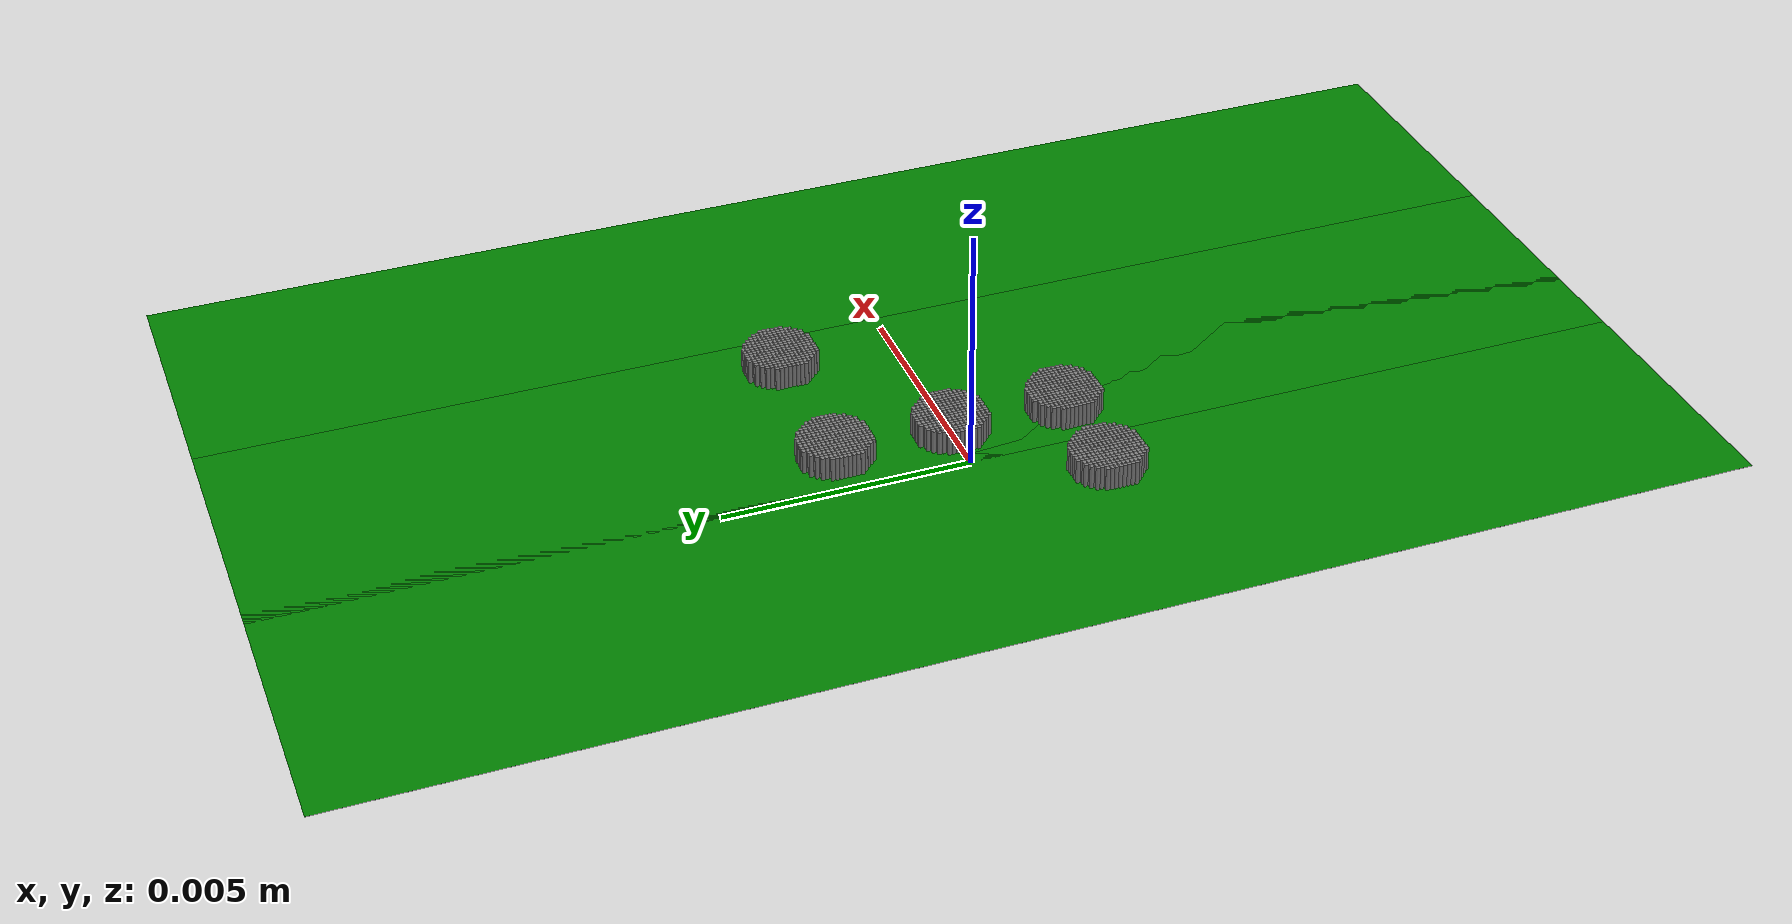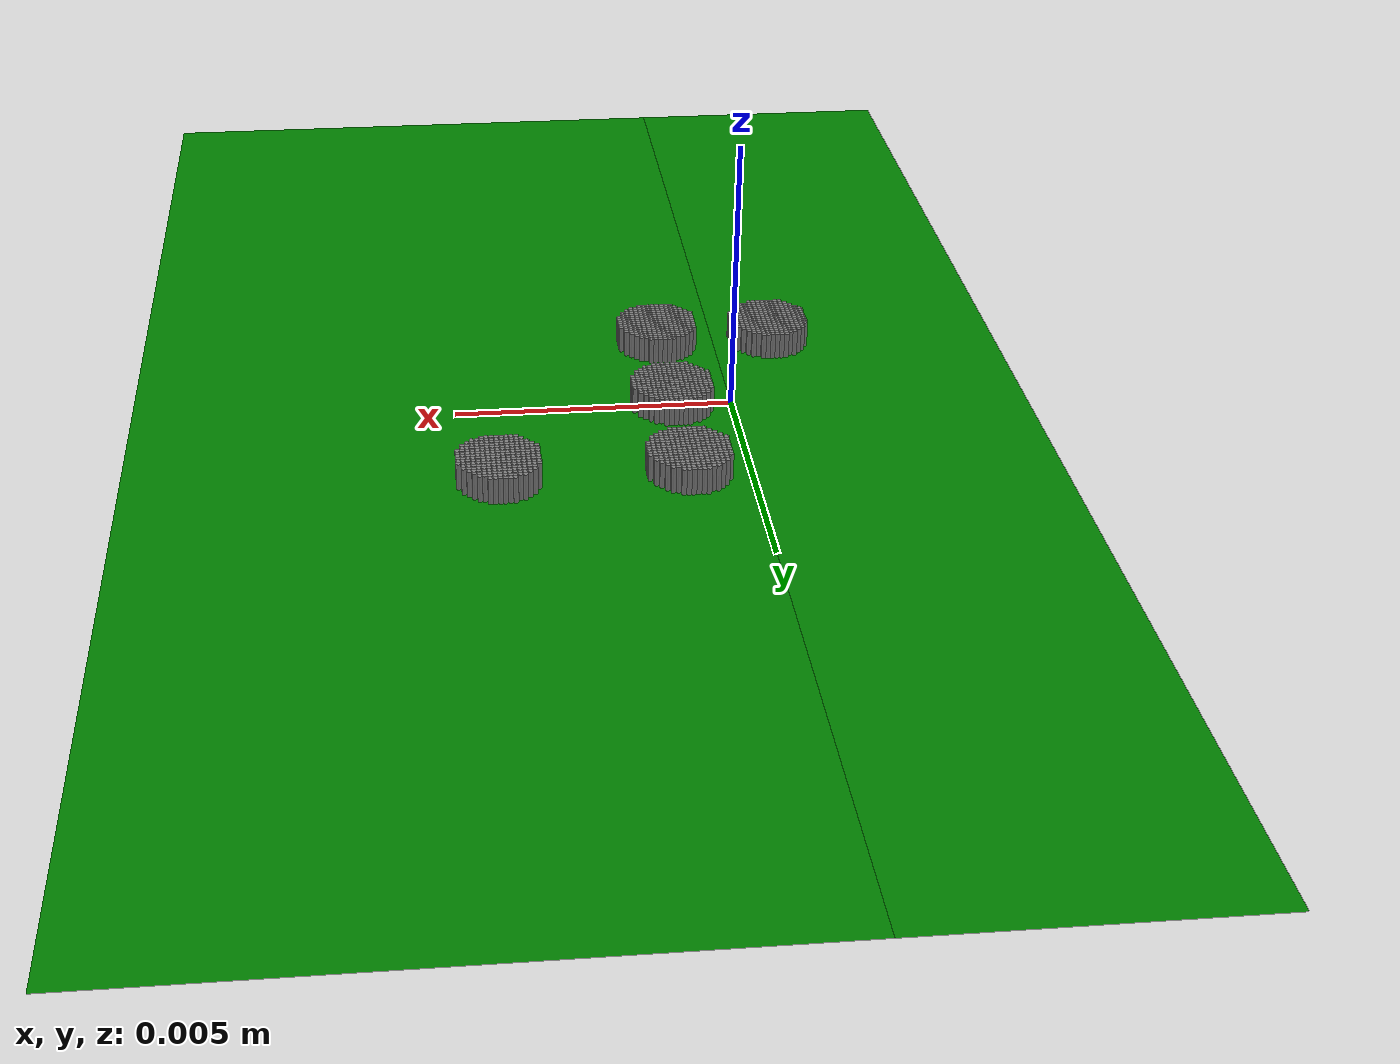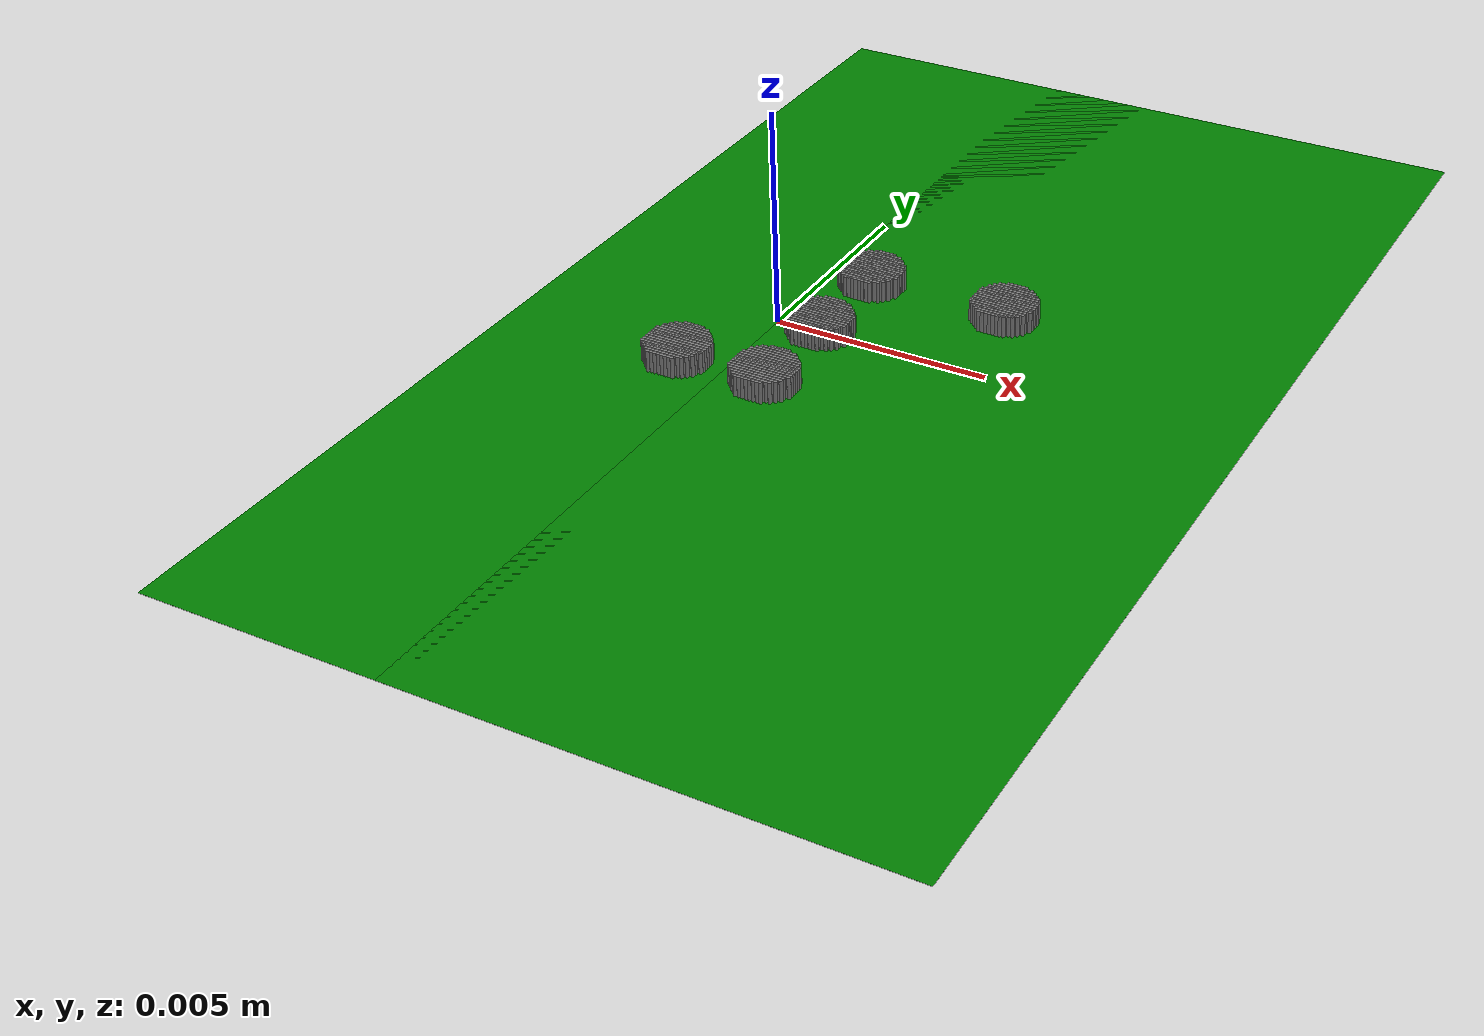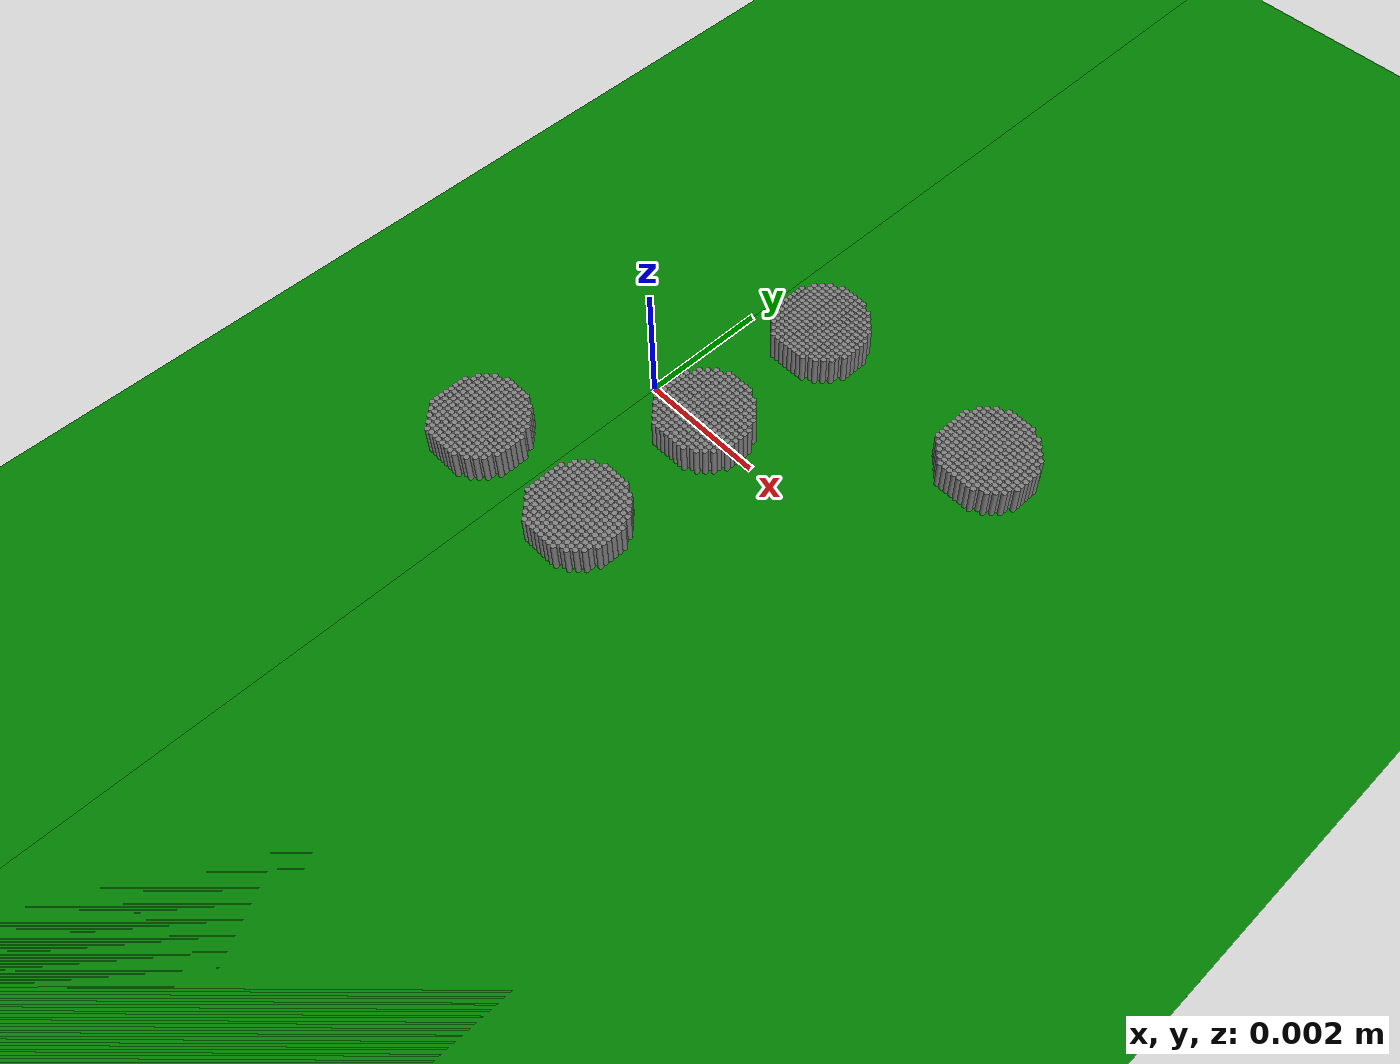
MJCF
<mujoco>
<worldbody>

<!--{NAME}.xml-->
<body pos='0 0 0'>
    <geom type='box' size='0.0054 0.013909999999999999 5e-07' rgba='0 0.5 0 1'/>
<body pos='-0.001065 -0.00237 0' name='l-bottom'>
    <geom type='cylinder' size='4.2904276540489165e-05 0.0005' pos='-0.0003209572345951085 -0.0006641914469190217 0'/>
<geom type='cylinder' size='4.2904276540489165e-05 0.0005' pos='-0.0002351486815141302 -0.0006641914469190217 0'/>
<geom type='cylinder' size='4.2904276540489165e-05 0.0005' pos='-0.0001493401284331519 -0.0006641914469190217 0'/>
<geom type='cylinder' size='4.2904276540489165e-05 0.0005' pos='-6.353157535217359e-05 -0.0006641914469190217 0'/>
<geom type='cylinder' size='4.2904276540489165e-05 0.0005' pos='2.2276977728804713e-05 -0.0006641914469190217 0'/>
<geom type='cylinder' size='4.2904276540489165e-05 0.0005' pos='0.00010808553080978302 -0.0006641914469190217 0'/>
<geom type='cylinder' size='4.2904276540489165e-05 0.0005' pos='0.00019389408389076132 -0.0006641914469190217 0'/>
<geom type='cylinder' size='4.2904276540489165e-05 0.0005' pos='0.0002797026369717396 -0.0006641914469190217 0'/>
<geom type='cylinder' size='4.2904276540489165e-05 0.0005' pos='-0.0004067657876760868 -0.0005783828938380434 0'/>
<geom type='cylinder' size='4.2904276540489165e-05 0.0005' pos='-0.0003209572345951085 -0.0005783828938380434 0'/>
<geom type='cylinder' size='4.2904276540489165e-05 0.0005' pos='-0.0002351486815141302 -0.0005783828938380434 0'/>
<geom type='cylinder' size='4.2904276540489165e-05 0.0005' pos='-0.0001493401284331519 -0.0005783828938380434 0'/>
<geom type='cylinder' size='4.2904276540489165e-05 0.0005' pos='-6.353157535217359e-05 -0.0005783828938380434 0'/>
<geom type='cylinder' size='4.2904276540489165e-05 0.0005' pos='2.2276977728804713e-05 -0.0005783828938380434 0'/>
<geom type='cylinder' size='4.2904276540489165e-05 0.0005' pos='0.00010808553080978302 -0.0005783828938380434 0'/>
<geom type='cylinder' size='4.2904276540489165e-05 0.0005' pos='0.00019389408389076132 -0.0005783828938380434 0'/>
<geom type='cylinder' size='4.2904276540489165e-05 0.0005' pos='0.0002797026369717396 -0.0005783828938380434 0'/>
<geom type='cylinder' size='4.2904276540489165e-05 0.0005' pos='0.0003655111900527179 -0.0005783828938380434 0'/>
<geom type='cylinder' size='4.2904276540489165e-05 0.0005' pos='0.00045131974313369623 -0.0005783828938380434 0'/>
<geom type='cylinder' size='4.2904276540489165e-05 0.0005' pos='-0.0004925743407570651 -0.0004925743407570651 0'/>
<geom type='cylinder' size='4.2904276540489165e-05 0.0005' pos='-0.0004067657876760868 -0.0004925743407570651 0'/>
<geom type='cylinder' size='4.2904276540489165e-05 0.0005' pos='-0.0003209572345951085 -0.0004925743407570651 0'/>
<geom type='cylinder' size='4.2904276540489165e-05 0.0005' pos='-0.0002351486815141302 -0.0004925743407570651 0'/>
<geom type='cylinder' size='4.2904276540489165e-05 0.0005' pos='-0.0001493401284331519 -0.0004925743407570651 0'/>
<geom type='cylinder' size='4.2904276540489165e-05 0.0005' pos='-6.353157535217359e-05 -0.0004925743407570651 0'/>
<geom type='cylinder' size='4.2904276540489165e-05 0.0005' pos='2.2276977728804713e-05 -0.0004925743407570651 0'/>
<geom type='cylinder' size='4.2904276540489165e-05 0.0005' pos='0.00010808553080978302 -0.0004925743407570651 0'/>
<geom type='cylinder' size='4.2904276540489165e-05 0.0005' pos='0.00019389408389076132 -0.0004925743407570651 0'/>
<geom type='cylinder' size='4.2904276540489165e-05 0.0005' pos='0.0002797026369717396 -0.0004925743407570651 0'/>
<geom type='cylinder' size='4.2904276540489165e-05 0.0005' pos='0.0003655111900527179 -0.0004925743407570651 0'/>
<geom type='cylinder' size='4.2904276540489165e-05 0.0005' pos='0.00045131974313369623 -0.0004925743407570651 0'/>
<geom type='cylinder' size='4.2904276540489165e-05 0.0005' pos='0.0005371282962146745 -0.0004925743407570651 0'/>
<geom type='cylinder' size='4.2904276540489165e-05 0.0005' pos='-0.0005783828938380434 -0.0004067657876760868 0'/>
<geom type='cylinder' size='4.2904276540489165e-05 0.0005' pos='-0.0004925743407570651 -0.0004067657876760868 0'/>
<geom type='cylinder' size='4.2904276540489165e-05 0.0005' pos='-0.0004067657876760868 -0.0004067657876760868 0'/>
<geom type='cylinder' size='4.2904276540489165e-05 0.0005' pos='-0.0003209572345951085 -0.0004067657876760868 0'/>
<geom type='cylinder' size='4.2904276540489165e-05 0.0005' pos='-0.0002351486815141302 -0.0004067657876760868 0'/>
<geom type='cylinder' size='4.2904276540489165e-05 0.0005' pos='-0.0001493401284331519 -0.0004067657876760868 0'/>
<geom type='cylinder' size='4.2904276540489165e-05 0.0005' pos='-6.353157535217359e-05 -0.0004067657876760868 0'/>
<geom type='cylinder' size='4.2904276540489165e-05 0.0005' pos='2.2276977728804713e-05 -0.0004067657876760868 0'/>
<geom type='cylinder' size='4.2904276540489165e-05 0.0005' pos='0.00010808553080978302 -0.0004067657876760868 0'/>
<geom type='cylinder' size='4.2904276540489165e-05 0.0005' pos='0.00019389408389076132 -0.0004067657876760868 0'/>
<geom type='cylinder' size='4.2904276540489165e-05 0.0005' pos='0.0002797026369717396 -0.0004067657876760868 0'/>
<geom type='cylinder' size='4.2904276540489165e-05 0.0005' pos='0.0003655111900527179 -0.0004067657876760868 0'/>
<geom type='cylinder' size='4.2904276540489165e-05 0.0005' pos='0.00045131974313369623 -0.0004067657876760868 0'/>
<geom type='cylinder' size='4.2904276540489165e-05 0.0005' pos='0.0005371282962146745 -0.0004067657876760868 0'/>
<geom type='cylinder' size='4.2904276540489165e-05 0.0005' pos='0.0006229368492956528 -0.0004067657876760868 0'/>
<geom type='cylinder' size='4.2904276540489165e-05 0.0005' pos='-0.0006641914469190217 -0.0003209572345951085 0'/>
<geom type='cylinder' size='4.2904276540489165e-05 0.0005' pos='-0.0005783828938380434 -0.0003209572345951085 0'/>
<geom type='cylinder' size='4.2904276540489165e-05 0.0005' pos='-0.0004925743407570651 -0.0003209572345951085 0'/>
<geom type='cylinder' size='4.2904276540489165e-05 0.0005' pos='-0.0004067657876760868 -0.0003209572345951085 0'/>
<geom type='cylinder' size='4.2904276540489165e-05 0.0005' pos='-0.0003209572345951085 -0.0003209572345951085 0'/>
<geom type='cylinder' size='4.2904276540489165e-05 0.0005' pos='-0.0002351486815141302 -0.0003209572345951085 0'/>
<geom type='cylinder' size='4.2904276540489165e-05 0.0005' pos='-0.0001493401284331519 -0.0003209572345951085 0'/>
<geom type='cylinder' size='4.2904276540489165e-05 0.0005' pos='-6.353157535217359e-05 -0.0003209572345951085 0'/>
<geom type='cylinder' size='4.2904276540489165e-05 0.0005' pos='2.2276977728804713e-05 -0.0003209572345951085 0'/>
<geom type='cylinder' size='4.2904276540489165e-05 0.0005' pos='0.00010808553080978302 -0.0003209572345951085 0'/>
<geom type='cylinder' size='4.2904276540489165e-05 0.0005' pos='0.00019389408389076132 -0.0003209572345951085 0'/>
<geom type='cylinder' size='4.2904276540489165e-05 0.0005' pos='0.0002797026369717396 -0.0003209572345951085 0'/>
<geom type='cylinder' size='4.2904276540489165e-05 0.0005' pos='0.0003655111900527179 -0.0003209572345951085 0'/>
<geom type='cylinder' size='4.2904276540489165e-05 0.0005' pos='0.00045131974313369623 -0.0003209572345951085 0'/>
<geom type='cylinder' size='4.2904276540489165e-05 0.0005' pos='0.0005371282962146745 -0.0003209572345951085 0'/>
<geom type='cylinder' size='4.2904276540489165e-05 0.0005' pos='0.0006229368492956528 -0.0003209572345951085 0'/>
<geom type='cylinder' size='4.2904276540489165e-05 0.0005' pos='-0.0006641914469190217 -0.0002351486815141302 0'/>
<geom type='cylinder' size='4.2904276540489165e-05 0.0005' pos='-0.0005783828938380434 -0.0002351486815141302 0'/>
<geom type='cylinder' size='4.2904276540489165e-05 0.0005' pos='-0.0004925743407570651 -0.0002351486815141302 0'/>
<geom type='cylinder' size='4.2904276540489165e-05 0.0005' pos='-0.0004067657876760868 -0.0002351486815141302 0'/>
<geom type='cylinder' size='4.2904276540489165e-05 0.0005' pos='-0.0003209572345951085 -0.0002351486815141302 0'/>
<geom type='cylinder' size='4.2904276540489165e-05 0.0005' pos='-0.0002351486815141302 -0.0002351486815141302 0'/>
<geom type='cylinder' size='4.2904276540489165e-05 0.0005' pos='-0.0001493401284331519 -0.0002351486815141302 0'/>
<geom type='cylinder' size='4.2904276540489165e-05 0.0005' pos='-6.353157535217359e-05 -0.0002351486815141302 0'/>
<geom type='cylinder' size='4.2904276540489165e-05 0.0005' pos='2.2276977728804713e-05 -0.0002351486815141302 0'/>
<geom type='cylinder' size='4.2904276540489165e-05 0.0005' pos='0.00010808553080978302 -0.0002351486815141302 0'/>
<geom type='cylinder' size='4.2904276540489165e-05 0.0005' pos='0.00019389408389076132 -0.0002351486815141302 0'/>
<geom type='cylinder' size='4.2904276540489165e-05 0.0005' pos='0.0002797026369717396 -0.0002351486815141302 0'/>
<geom type='cylinder' size='4.2904276540489165e-05 0.0005' pos='0.0003655111900527179 -0.0002351486815141302 0'/>
<geom type='cylinder' size='4.2904276540489165e-05 0.0005' pos='0.00045131974313369623 -0.0002351486815141302 0'/>
<geom type='cylinder' size='4.2904276540489165e-05 0.0005' pos='0.0005371282962146745 -0.0002351486815141302 0'/>
<geom type='cylinder' size='4.2904276540489165e-05 0.0005' pos='0.0006229368492956528 -0.0002351486815141302 0'/>
<geom type='cylinder' size='4.2904276540489165e-05 0.0005' pos='0.0007087454023766311 -0.0002351486815141302 0'/>
<geom type='cylinder' size='4.2904276540489165e-05 0.0005' pos='-0.0006641914469190217 -0.0001493401284331519 0'/>
<geom type='cylinder' size='4.2904276540489165e-05 0.0005' pos='-0.0005783828938380434 -0.0001493401284331519 0'/>
<geom type='cylinder' size='4.2904276540489165e-05 0.0005' pos='-0.0004925743407570651 -0.0001493401284331519 0'/>
<geom type='cylinder' size='4.2904276540489165e-05 0.0005' pos='-0.0004067657876760868 -0.0001493401284331519 0'/>
<geom type='cylinder' size='4.2904276540489165e-05 0.0005' pos='-0.0003209572345951085 -0.0001493401284331519 0'/>
<geom type='cylinder' size='4.2904276540489165e-05 0.0005' pos='-0.0002351486815141302 -0.0001493401284331519 0'/>
<geom type='cylinder' size='4.2904276540489165e-05 0.0005' pos='-0.0001493401284331519 -0.0001493401284331519 0'/>
<geom type='cylinder' size='4.2904276540489165e-05 0.0005' pos='-6.353157535217359e-05 -0.0001493401284331519 0'/>
<geom type='cylinder' size='4.2904276540489165e-05 0.0005' pos='2.2276977728804713e-05 -0.0001493401284331519 0'/>
<geom type='cylinder' size='4.2904276540489165e-05 0.0005' pos='0.00010808553080978302 -0.0001493401284331519 0'/>
<geom type='cylinder' size='4.2904276540489165e-05 0.0005' pos='0.00019389408389076132 -0.0001493401284331519 0'/>
<geom type='cylinder' size='4.2904276540489165e-05 0.0005' pos='0.0002797026369717396 -0.0001493401284331519 0'/>
<geom type='cylinder' size='4.2904276540489165e-05 0.0005' pos='0.0003655111900527179 -0.0001493401284331519 0'/>
<geom type='cylinder' size='4.2904276540489165e-05 0.0005' pos='0.00045131974313369623 -0.0001493401284331519 0'/>
<geom type='cylinder' size='4.2904276540489165e-05 0.0005' pos='0.0005371282962146745 -0.0001493401284331519 0'/>
<geom type='cylinder' size='4.2904276540489165e-05 0.0005' pos='0.0006229368492956528 -0.0001493401284331519 0'/>
<geom type='cylinder' size='4.2904276540489165e-05 0.0005' pos='0.0007087454023766311 -0.0001493401284331519 0'/>
<geom type='cylinder' size='4.2904276540489165e-05 0.0005' pos='-0.0006641914469190217 -6.353157535217359e-05 0'/>
<geom type='cylinder' size='4.2904276540489165e-05 0.0005' pos='-0.0005783828938380434 -6.353157535217359e-05 0'/>
<geom type='cylinder' size='4.2904276540489165e-05 0.0005' pos='-0.0004925743407570651 -6.353157535217359e-05 0'/>
<geom type='cylinder' size='4.2904276540489165e-05 0.0005' pos='-0.0004067657876760868 -6.353157535217359e-05 0'/>
<geom type='cylinder' size='4.2904276540489165e-05 0.0005' pos='-0.0003209572345951085 -6.353157535217359e-05 0'/>
<geom type='cylinder' size='4.2904276540489165e-05 0.0005' pos='-0.0002351486815141302 -6.353157535217359e-05 0'/>
<geom type='cylinder' size='4.2904276540489165e-05 0.0005' pos='-0.0001493401284331519 -6.353157535217359e-05 0'/>
<geom type='cylinder' size='4.2904276540489165e-05 0.0005' pos='-6.353157535217359e-05 -6.353157535217359e-05 0'/>
<geom type='cylinder' size='4.2904276540489165e-05 0.0005' pos='2.2276977728804713e-05 -6.353157535217359e-05 0'/>
<geom type='cylinder' size='4.2904276540489165e-05 0.0005' pos='0.00010808553080978302 -6.353157535217359e-05 0'/>
<geom type='cylinder' size='4.2904276540489165e-05 0.0005' pos='0.00019389408389076132 -6.353157535217359e-05 0'/>
<geom type='cylinder' size='4.2904276540489165e-05 0.0005' pos='0.0002797026369717396 -6.353157535217359e-05 0'/>
<geom type='cylinder' size='4.2904276540489165e-05 0.0005' pos='0.0003655111900527179 -6.353157535217359e-05 0'/>
<geom type='cylinder' size='4.2904276540489165e-05 0.0005' pos='0.00045131974313369623 -6.353157535217359e-05 0'/>
<geom type='cylinder' size='4.2904276540489165e-05 0.0005' pos='0.0005371282962146745 -6.353157535217359e-05 0'/>
<geom type='cylinder' size='4.2904276540489165e-05 0.0005' pos='0.0006229368492956528 -6.353157535217359e-05 0'/>
<geom type='cylinder' size='4.2904276540489165e-05 0.0005' pos='0.0007087454023766311 -6.353157535217359e-05 0'/>
<geom type='cylinder' size='4.2904276540489165e-05 0.0005' pos='-0.0006641914469190217 2.2276977728804713e-05 0'/>
<geom type='cylinder' size='4.2904276540489165e-05 0.0005' pos='-0.0005783828938380434 2.2276977728804713e-05 0'/>
<geom type='cylinder' size='4.2904276540489165e-05 0.0005' pos='-0.0004925743407570651 2.2276977728804713e-05 0'/>
<geom type='cylinder' size='4.2904276540489165e-05 0.0005' pos='-0.0004067657876760868 2.2276977728804713e-05 0'/>
<geom type='cylinder' size='4.2904276540489165e-05 0.0005' pos='-0.0003209572345951085 2.2276977728804713e-05 0'/>
<geom type='cylinder' size='4.2904276540489165e-05 0.0005' pos='-0.0002351486815141302 2.2276977728804713e-05 0'/>
<geom type='cylinder' size='4.2904276540489165e-05 0.0005' pos='-0.0001493401284331519 2.2276977728804713e-05 0'/>
<geom type='cylinder' size='4.2904276540489165e-05 0.0005' pos='-6.353157535217359e-05 2.2276977728804713e-05 0'/>
<geom type='cylinder' size='4.2904276540489165e-05 0.0005' pos='2.2276977728804713e-05 2.2276977728804713e-05 0'/>
<geom type='cylinder' size='4.2904276540489165e-05 0.0005' pos='0.00010808553080978302 2.2276977728804713e-05 0'/>
<geom type='cylinder' size='4.2904276540489165e-05 0.0005' pos='0.00019389408389076132 2.2276977728804713e-05 0'/>
<geom type='cylinder' size='4.2904276540489165e-05 0.0005' pos='0.0002797026369717396 2.2276977728804713e-05 0'/>
<geom type='cylinder' size='4.2904276540489165e-05 0.0005' pos='0.0003655111900527179 2.2276977728804713e-05 0'/>
<geom type='cylinder' size='4.2904276540489165e-05 0.0005' pos='0.00045131974313369623 2.2276977728804713e-05 0'/>
<geom type='cylinder' size='4.2904276540489165e-05 0.0005' pos='0.0005371282962146745 2.2276977728804713e-05 0'/>
<geom type='cylinder' size='4.2904276540489165e-05 0.0005' pos='0.0006229368492956528 2.2276977728804713e-05 0'/>
<geom type='cylinder' size='4.2904276540489165e-05 0.0005' pos='0.0007087454023766311 2.2276977728804713e-05 0'/>
<geom type='cylinder' size='4.2904276540489165e-05 0.0005' pos='-0.0006641914469190217 0.00010808553080978302 0'/>
<geom type='cylinder' size='4.2904276540489165e-05 0.0005' pos='-0.0005783828938380434 0.00010808553080978302 0'/>
<geom type='cylinder' size='4.2904276540489165e-05 0.0005' pos='-0.0004925743407570651 0.00010808553080978302 0'/>
<geom type='cylinder' size='4.2904276540489165e-05 0.0005' pos='-0.0004067657876760868 0.00010808553080978302 0'/>
<geom type='cylinder' size='4.2904276540489165e-05 0.0005' pos='-0.0003209572345951085 0.00010808553080978302 0'/>
<geom type='cylinder' size='4.2904276540489165e-05 0.0005' pos='-0.0002351486815141302 0.00010808553080978302 0'/>
<geom type='cylinder' size='4.2904276540489165e-05 0.0005' pos='-0.0001493401284331519 0.00010808553080978302 0'/>
<geom type='cylinder' size='4.2904276540489165e-05 0.0005' pos='-6.353157535217359e-05 0.00010808553080978302 0'/>
<geom type='cylinder' size='4.2904276540489165e-05 0.0005' pos='2.2276977728804713e-05 0.00010808553080978302 0'/>
<geom type='cylinder' size='4.2904276540489165e-05 0.0005' pos='0.00010808553080978302 0.00010808553080978302 0'/>
<geom type='cylinder' size='4.2904276540489165e-05 0.0005' pos='0.00019389408389076132 0.00010808553080978302 0'/>
<geom type='cylinder' size='4.2904276540489165e-05 0.0005' pos='0.0002797026369717396 0.00010808553080978302 0'/>
<geom type='cylinder' size='4.2904276540489165e-05 0.0005' pos='0.0003655111900527179 0.00010808553080978302 0'/>
<geom type='cylinder' size='4.2904276540489165e-05 0.0005' pos='0.00045131974313369623 0.00010808553080978302 0'/>
<geom type='cylinder' size='4.2904276540489165e-05 0.0005' pos='0.0005371282962146745 0.00010808553080978302 0'/>
<geom type='cylinder' size='4.2904276540489165e-05 0.0005' pos='0.0006229368492956528 0.00010808553080978302 0'/>
<geom type='cylinder' size='4.2904276540489165e-05 0.0005' pos='0.0007087454023766311 0.00010808553080978302 0'/>
<geom type='cylinder' size='4.2904276540489165e-05 0.0005' pos='-0.0006641914469190217 0.00019389408389076132 0'/>
<geom type='cylinder' size='4.2904276540489165e-05 0.0005' pos='-0.0005783828938380434 0.00019389408389076132 0'/>
<geom type='cylinder' size='4.2904276540489165e-05 0.0005' pos='-0.0004925743407570651 0.00019389408389076132 0'/>
<geom type='cylinder' size='4.2904276540489165e-05 0.0005' pos='-0.0004067657876760868 0.00019389408389076132 0'/>
<geom type='cylinder' size='4.2904276540489165e-05 0.0005' pos='-0.0003209572345951085 0.00019389408389076132 0'/>
<geom type='cylinder' size='4.2904276540489165e-05 0.0005' pos='-0.0002351486815141302 0.00019389408389076132 0'/>
<geom type='cylinder' size='4.2904276540489165e-05 0.0005' pos='-0.0001493401284331519 0.00019389408389076132 0'/>
<geom type='cylinder' size='4.2904276540489165e-05 0.0005' pos='-6.353157535217359e-05 0.00019389408389076132 0'/>
<geom type='cylinder' size='4.2904276540489165e-05 0.0005' pos='2.2276977728804713e-05 0.00019389408389076132 0'/>
<geom type='cylinder' size='4.2904276540489165e-05 0.0005' pos='0.00010808553080978302 0.00019389408389076132 0'/>
<geom type='cylinder' size='4.2904276540489165e-05 0.0005' pos='0.00019389408389076132 0.00019389408389076132 0'/>
<geom type='cylinder' size='4.2904276540489165e-05 0.0005' pos='0.0002797026369717396 0.00019389408389076132 0'/>
<geom type='cylinder' size='4.2904276540489165e-05 0.0005' pos='0.0003655111900527179 0.00019389408389076132 0'/>
<geom type='cylinder' size='4.2904276540489165e-05 0.0005' pos='0.00045131974313369623 0.00019389408389076132 0'/>
<geom type='cylinder' size='4.2904276540489165e-05 0.0005' pos='0.0005371282962146745 0.00019389408389076132 0'/>
<geom type='cylinder' size='4.2904276540489165e-05 0.0005' pos='0.0006229368492956528 0.00019389408389076132 0'/>
<geom type='cylinder' size='4.2904276540489165e-05 0.0005' pos='0.0007087454023766311 0.00019389408389076132 0'/>
<geom type='cylinder' size='4.2904276540489165e-05 0.0005' pos='-0.0006641914469190217 0.0002797026369717396 0'/>
<geom type='cylinder' size='4.2904276540489165e-05 0.0005' pos='-0.0005783828938380434 0.0002797026369717396 0'/>
<geom type='cylinder' size='4.2904276540489165e-05 0.0005' pos='-0.0004925743407570651 0.0002797026369717396 0'/>
<geom type='cylinder' size='4.2904276540489165e-05 0.0005' pos='-0.0004067657876760868 0.0002797026369717396 0'/>
<geom type='cylinder' size='4.2904276540489165e-05 0.0005' pos='-0.0003209572345951085 0.0002797026369717396 0'/>
<geom type='cylinder' size='4.2904276540489165e-05 0.0005' pos='-0.0002351486815141302 0.0002797026369717396 0'/>
<geom type='cylinder' size='4.2904276540489165e-05 0.0005' pos='-0.0001493401284331519 0.0002797026369717396 0'/>
<geom type='cylinder' size='4.2904276540489165e-05 0.0005' pos='-6.353157535217359e-05 0.0002797026369717396 0'/>
<geom type='cylinder' size='4.2904276540489165e-05 0.0005' pos='2.2276977728804713e-05 0.0002797026369717396 0'/>
<geom type='cylinder' size='4.2904276540489165e-05 0.0005' pos='0.00010808553080978302 0.0002797026369717396 0'/>
<geom type='cylinder' size='4.2904276540489165e-05 0.0005' pos='0.00019389408389076132 0.0002797026369717396 0'/>
<geom type='cylinder' size='4.2904276540489165e-05 0.0005' pos='0.0002797026369717396 0.0002797026369717396 0'/>
<geom type='cylinder' size='4.2904276540489165e-05 0.0005' pos='0.0003655111900527179 0.0002797026369717396 0'/>
<geom type='cylinder' size='4.2904276540489165e-05 0.0005' pos='0.00045131974313369623 0.0002797026369717396 0'/>
<geom type='cylinder' size='4.2904276540489165e-05 0.0005' pos='0.0005371282962146745 0.0002797026369717396 0'/>
<geom type='cylinder' size='4.2904276540489165e-05 0.0005' pos='0.0006229368492956528 0.0002797026369717396 0'/>
<geom type='cylinder' size='4.2904276540489165e-05 0.0005' pos='-0.0005783828938380434 0.0003655111900527179 0'/>
<geom type='cylinder' size='4.2904276540489165e-05 0.0005' pos='-0.0004925743407570651 0.0003655111900527179 0'/>
<geom type='cylinder' size='4.2904276540489165e-05 0.0005' pos='-0.0004067657876760868 0.0003655111900527179 0'/>
<geom type='cylinder' size='4.2904276540489165e-05 0.0005' pos='-0.0003209572345951085 0.0003655111900527179 0'/>
<geom type='cylinder' size='4.2904276540489165e-05 0.0005' pos='-0.0002351486815141302 0.0003655111900527179 0'/>
<geom type='cylinder' size='4.2904276540489165e-05 0.0005' pos='-0.0001493401284331519 0.0003655111900527179 0'/>
<geom type='cylinder' size='4.2904276540489165e-05 0.0005' pos='-6.353157535217359e-05 0.0003655111900527179 0'/>
<geom type='cylinder' size='4.2904276540489165e-05 0.0005' pos='2.2276977728804713e-05 0.0003655111900527179 0'/>
<geom type='cylinder' size='4.2904276540489165e-05 0.0005' pos='0.00010808553080978302 0.0003655111900527179 0'/>
<geom type='cylinder' size='4.2904276540489165e-05 0.0005' pos='0.00019389408389076132 0.0003655111900527179 0'/>
<geom type='cylinder' size='4.2904276540489165e-05 0.0005' pos='0.0002797026369717396 0.0003655111900527179 0'/>
<geom type='cylinder' size='4.2904276540489165e-05 0.0005' pos='0.0003655111900527179 0.0003655111900527179 0'/>
<geom type='cylinder' size='4.2904276540489165e-05 0.0005' pos='0.00045131974313369623 0.0003655111900527179 0'/>
<geom type='cylinder' size='4.2904276540489165e-05 0.0005' pos='0.0005371282962146745 0.0003655111900527179 0'/>
<geom type='cylinder' size='4.2904276540489165e-05 0.0005' pos='0.0006229368492956528 0.0003655111900527179 0'/>
<geom type='cylinder' size='4.2904276540489165e-05 0.0005' pos='-0.0005783828938380434 0.00045131974313369623 0'/>
<geom type='cylinder' size='4.2904276540489165e-05 0.0005' pos='-0.0004925743407570651 0.00045131974313369623 0'/>
<geom type='cylinder' size='4.2904276540489165e-05 0.0005' pos='-0.0004067657876760868 0.00045131974313369623 0'/>
<geom type='cylinder' size='4.2904276540489165e-05 0.0005' pos='-0.0003209572345951085 0.00045131974313369623 0'/>
<geom type='cylinder' size='4.2904276540489165e-05 0.0005' pos='-0.0002351486815141302 0.00045131974313369623 0'/>
<geom type='cylinder' size='4.2904276540489165e-05 0.0005' pos='-0.0001493401284331519 0.00045131974313369623 0'/>
<geom type='cylinder' size='4.2904276540489165e-05 0.0005' pos='-6.353157535217359e-05 0.00045131974313369623 0'/>
<geom type='cylinder' size='4.2904276540489165e-05 0.0005' pos='2.2276977728804713e-05 0.00045131974313369623 0'/>
<geom type='cylinder' size='4.2904276540489165e-05 0.0005' pos='0.00010808553080978302 0.00045131974313369623 0'/>
<geom type='cylinder' size='4.2904276540489165e-05 0.0005' pos='0.00019389408389076132 0.00045131974313369623 0'/>
<geom type='cylinder' size='4.2904276540489165e-05 0.0005' pos='0.0002797026369717396 0.00045131974313369623 0'/>
<geom type='cylinder' size='4.2904276540489165e-05 0.0005' pos='0.0003655111900527179 0.00045131974313369623 0'/>
<geom type='cylinder' size='4.2904276540489165e-05 0.0005' pos='0.00045131974313369623 0.00045131974313369623 0'/>
<geom type='cylinder' size='4.2904276540489165e-05 0.0005' pos='0.0005371282962146745 0.00045131974313369623 0'/>
<geom type='cylinder' size='4.2904276540489165e-05 0.0005' pos='-0.0004925743407570651 0.0005371282962146745 0'/>
<geom type='cylinder' size='4.2904276540489165e-05 0.0005' pos='-0.0004067657876760868 0.0005371282962146745 0'/>
<geom type='cylinder' size='4.2904276540489165e-05 0.0005' pos='-0.0003209572345951085 0.0005371282962146745 0'/>
<geom type='cylinder' size='4.2904276540489165e-05 0.0005' pos='-0.0002351486815141302 0.0005371282962146745 0'/>
<geom type='cylinder' size='4.2904276540489165e-05 0.0005' pos='-0.0001493401284331519 0.0005371282962146745 0'/>
<geom type='cylinder' size='4.2904276540489165e-05 0.0005' pos='-6.353157535217359e-05 0.0005371282962146745 0'/>
<geom type='cylinder' size='4.2904276540489165e-05 0.0005' pos='2.2276977728804713e-05 0.0005371282962146745 0'/>
<geom type='cylinder' size='4.2904276540489165e-05 0.0005' pos='0.00010808553080978302 0.0005371282962146745 0'/>
<geom type='cylinder' size='4.2904276540489165e-05 0.0005' pos='0.00019389408389076132 0.0005371282962146745 0'/>
<geom type='cylinder' size='4.2904276540489165e-05 0.0005' pos='0.0002797026369717396 0.0005371282962146745 0'/>
<geom type='cylinder' size='4.2904276540489165e-05 0.0005' pos='0.0003655111900527179 0.0005371282962146745 0'/>
<geom type='cylinder' size='4.2904276540489165e-05 0.0005' pos='0.00045131974313369623 0.0005371282962146745 0'/>
<geom type='cylinder' size='4.2904276540489165e-05 0.0005' pos='-0.0004067657876760868 0.0006229368492956528 0'/>
<geom type='cylinder' size='4.2904276540489165e-05 0.0005' pos='-0.0003209572345951085 0.0006229368492956528 0'/>
<geom type='cylinder' size='4.2904276540489165e-05 0.0005' pos='-0.0002351486815141302 0.0006229368492956528 0'/>
<geom type='cylinder' size='4.2904276540489165e-05 0.0005' pos='-0.0001493401284331519 0.0006229368492956528 0'/>
<geom type='cylinder' size='4.2904276540489165e-05 0.0005' pos='-6.353157535217359e-05 0.0006229368492956528 0'/>
<geom type='cylinder' size='4.2904276540489165e-05 0.0005' pos='2.2276977728804713e-05 0.0006229368492956528 0'/>
<geom type='cylinder' size='4.2904276540489165e-05 0.0005' pos='0.00010808553080978302 0.0006229368492956528 0'/>
<geom type='cylinder' size='4.2904276540489165e-05 0.0005' pos='0.00019389408389076132 0.0006229368492956528 0'/>
<geom type='cylinder' size='4.2904276540489165e-05 0.0005' pos='0.0002797026369717396 0.0006229368492956528 0'/>
<geom type='cylinder' size='4.2904276540489165e-05 0.0005' pos='0.0003655111900527179 0.0006229368492956528 0'/>
<geom type='cylinder' size='4.2904276540489165e-05 0.0005' pos='-0.0002351486815141302 0.0007087454023766311 0'/>
<geom type='cylinder' size='4.2904276540489165e-05 0.0005' pos='-0.0001493401284331519 0.0007087454023766311 0'/>
<geom type='cylinder' size='4.2904276540489165e-05 0.0005' pos='-6.353157535217359e-05 0.0007087454023766311 0'/>
<geom type='cylinder' size='4.2904276540489165e-05 0.0005' pos='2.2276977728804713e-05 0.0007087454023766311 0'/>
<geom type='cylinder' size='4.2904276540489165e-05 0.0005' pos='0.00010808553080978302 0.0007087454023766311 0'/>
<geom type='cylinder' size='4.2904276540489165e-05 0.0005' pos='0.00019389408389076132 0.0007087454023766311 0'/>

</body>
<body pos='0.001065 0.00237 0' name='r-top'>
    <geom type='cylinder' size='4.2904276540489165e-05 0.0005' pos='-0.0003209572345951085 -0.0006641914469190217 0'/>
<geom type='cylinder' size='4.2904276540489165e-05 0.0005' pos='-0.0002351486815141302 -0.0006641914469190217 0'/>
<geom type='cylinder' size='4.2904276540489165e-05 0.0005' pos='-0.0001493401284331519 -0.0006641914469190217 0'/>
<geom type='cylinder' size='4.2904276540489165e-05 0.0005' pos='-6.353157535217359e-05 -0.0006641914469190217 0'/>
<geom type='cylinder' size='4.2904276540489165e-05 0.0005' pos='2.2276977728804713e-05 -0.0006641914469190217 0'/>
<geom type='cylinder' size='4.2904276540489165e-05 0.0005' pos='0.00010808553080978302 -0.0006641914469190217 0'/>
<geom type='cylinder' size='4.2904276540489165e-05 0.0005' pos='0.00019389408389076132 -0.0006641914469190217 0'/>
<geom type='cylinder' size='4.2904276540489165e-05 0.0005' pos='0.0002797026369717396 -0.0006641914469190217 0'/>
<geom type='cylinder' size='4.2904276540489165e-05 0.0005' pos='-0.0004067657876760868 -0.0005783828938380434 0'/>
<geom type='cylinder' size='4.2904276540489165e-05 0.0005' pos='-0.0003209572345951085 -0.0005783828938380434 0'/>
<geom type='cylinder' size='4.2904276540489165e-05 0.0005' pos='-0.0002351486815141302 -0.0005783828938380434 0'/>
<geom type='cylinder' size='4.2904276540489165e-05 0.0005' pos='-0.0001493401284331519 -0.0005783828938380434 0'/>
<geom type='cylinder' size='4.2904276540489165e-05 0.0005' pos='-6.353157535217359e-05 -0.0005783828938380434 0'/>
<geom type='cylinder' size='4.2904276540489165e-05 0.0005' pos='2.2276977728804713e-05 -0.0005783828938380434 0'/>
<geom type='cylinder' size='4.2904276540489165e-05 0.0005' pos='0.00010808553080978302 -0.0005783828938380434 0'/>
<geom type='cylinder' size='4.2904276540489165e-05 0.0005' pos='0.00019389408389076132 -0.0005783828938380434 0'/>
<geom type='cylinder' size='4.2904276540489165e-05 0.0005' pos='0.0002797026369717396 -0.0005783828938380434 0'/>
<geom type='cylinder' size='4.2904276540489165e-05 0.0005' pos='0.0003655111900527179 -0.0005783828938380434 0'/>
<geom type='cylinder' size='4.2904276540489165e-05 0.0005' pos='0.00045131974313369623 -0.0005783828938380434 0'/>
<geom type='cylinder' size='4.2904276540489165e-05 0.0005' pos='-0.0004925743407570651 -0.0004925743407570651 0'/>
<geom type='cylinder' size='4.2904276540489165e-05 0.0005' pos='-0.0004067657876760868 -0.0004925743407570651 0'/>
<geom type='cylinder' size='4.2904276540489165e-05 0.0005' pos='-0.0003209572345951085 -0.0004925743407570651 0'/>
<geom type='cylinder' size='4.2904276540489165e-05 0.0005' pos='-0.0002351486815141302 -0.0004925743407570651 0'/>
<geom type='cylinder' size='4.2904276540489165e-05 0.0005' pos='-0.0001493401284331519 -0.0004925743407570651 0'/>
<geom type='cylinder' size='4.2904276540489165e-05 0.0005' pos='-6.353157535217359e-05 -0.0004925743407570651 0'/>
<geom type='cylinder' size='4.2904276540489165e-05 0.0005' pos='2.2276977728804713e-05 -0.0004925743407570651 0'/>
<geom type='cylinder' size='4.2904276540489165e-05 0.0005' pos='0.00010808553080978302 -0.0004925743407570651 0'/>
<geom type='cylinder' size='4.2904276540489165e-05 0.0005' pos='0.00019389408389076132 -0.0004925743407570651 0'/>
<geom type='cylinder' size='4.2904276540489165e-05 0.0005' pos='0.0002797026369717396 -0.0004925743407570651 0'/>
<geom type='cylinder' size='4.2904276540489165e-05 0.0005' pos='0.0003655111900527179 -0.0004925743407570651 0'/>
<geom type='cylinder' size='4.2904276540489165e-05 0.0005' pos='0.00045131974313369623 -0.0004925743407570651 0'/>
<geom type='cylinder' size='4.2904276540489165e-05 0.0005' pos='0.0005371282962146745 -0.0004925743407570651 0'/>
<geom type='cylinder' size='4.2904276540489165e-05 0.0005' pos='-0.0005783828938380434 -0.0004067657876760868 0'/>
<geom type='cylinder' size='4.2904276540489165e-05 0.0005' pos='-0.0004925743407570651 -0.0004067657876760868 0'/>
<geom type='cylinder' size='4.2904276540489165e-05 0.0005' pos='-0.0004067657876760868 -0.0004067657876760868 0'/>
<geom type='cylinder' size='4.2904276540489165e-05 0.0005' pos='-0.0003209572345951085 -0.0004067657876760868 0'/>
<geom type='cylinder' size='4.2904276540489165e-05 0.0005' pos='-0.0002351486815141302 -0.0004067657876760868 0'/>
<geom type='cylinder' size='4.2904276540489165e-05 0.0005' pos='-0.0001493401284331519 -0.0004067657876760868 0'/>
<geom type='cylinder' size='4.2904276540489165e-05 0.0005' pos='-6.353157535217359e-05 -0.0004067657876760868 0'/>
<geom type='cylinder' size='4.2904276540489165e-05 0.0005' pos='2.2276977728804713e-05 -0.0004067657876760868 0'/>
<geom type='cylinder' size='4.2904276540489165e-05 0.0005' pos='0.00010808553080978302 -0.0004067657876760868 0'/>
<geom type='cylinder' size='4.2904276540489165e-05 0.0005' pos='0.00019389408389076132 -0.0004067657876760868 0'/>
<geom type='cylinder' size='4.2904276540489165e-05 0.0005' pos='0.0002797026369717396 -0.0004067657876760868 0'/>
<geom type='cylinder' size='4.2904276540489165e-05 0.0005' pos='0.0003655111900527179 -0.0004067657876760868 0'/>
<geom type='cylinder' size='4.2904276540489165e-05 0.0005' pos='0.00045131974313369623 -0.0004067657876760868 0'/>
<geom type='cylinder' size='4.2904276540489165e-05 0.0005' pos='0.0005371282962146745 -0.0004067657876760868 0'/>
<geom type='cylinder' size='4.2904276540489165e-05 0.0005' pos='0.0006229368492956528 -0.0004067657876760868 0'/>
<geom type='cylinder' size='4.2904276540489165e-05 0.0005' pos='-0.0006641914469190217 -0.0003209572345951085 0'/>
<geom type='cylinder' size='4.2904276540489165e-05 0.0005' pos='-0.0005783828938380434 -0.0003209572345951085 0'/>
<geom type='cylinder' size='4.2904276540489165e-05 0.0005' pos='-0.0004925743407570651 -0.0003209572345951085 0'/>
<geom type='cylinder' size='4.2904276540489165e-05 0.0005' pos='-0.0004067657876760868 -0.0003209572345951085 0'/>
<geom type='cylinder' size='4.2904276540489165e-05 0.0005' pos='-0.0003209572345951085 -0.0003209572345951085 0'/>
<geom type='cylinder' size='4.2904276540489165e-05 0.0005' pos='-0.0002351486815141302 -0.0003209572345951085 0'/>
<geom type='cylinder' size='4.2904276540489165e-05 0.0005' pos='-0.0001493401284331519 -0.0003209572345951085 0'/>
<geom type='cylinder' size='4.2904276540489165e-05 0.0005' pos='-6.353157535217359e-05 -0.0003209572345951085 0'/>
<geom type='cylinder' size='4.2904276540489165e-05 0.0005' pos='2.2276977728804713e-05 -0.0003209572345951085 0'/>
<geom type='cylinder' size='4.2904276540489165e-05 0.0005' pos='0.00010808553080978302 -0.0003209572345951085 0'/>
<geom type='cylinder' size='4.2904276540489165e-05 0.0005' pos='0.00019389408389076132 -0.0003209572345951085 0'/>
<geom type='cylinder' size='4.2904276540489165e-05 0.0005' pos='0.0002797026369717396 -0.0003209572345951085 0'/>
<geom type='cylinder' size='4.2904276540489165e-05 0.0005' pos='0.0003655111900527179 -0.0003209572345951085 0'/>
<geom type='cylinder' size='4.2904276540489165e-05 0.0005' pos='0.00045131974313369623 -0.0003209572345951085 0'/>
<geom type='cylinder' size='4.2904276540489165e-05 0.0005' pos='0.0005371282962146745 -0.0003209572345951085 0'/>
<geom type='cylinder' size='4.2904276540489165e-05 0.0005' pos='0.0006229368492956528 -0.0003209572345951085 0'/>
<geom type='cylinder' size='4.2904276540489165e-05 0.0005' pos='-0.0006641914469190217 -0.0002351486815141302 0'/>
<geom type='cylinder' size='4.2904276540489165e-05 0.0005' pos='-0.0005783828938380434 -0.0002351486815141302 0'/>
<geom type='cylinder' size='4.2904276540489165e-05 0.0005' pos='-0.0004925743407570651 -0.0002351486815141302 0'/>
<geom type='cylinder' size='4.2904276540489165e-05 0.0005' pos='-0.0004067657876760868 -0.0002351486815141302 0'/>
<geom type='cylinder' size='4.2904276540489165e-05 0.0005' pos='-0.0003209572345951085 -0.0002351486815141302 0'/>
<geom type='cylinder' size='4.2904276540489165e-05 0.0005' pos='-0.0002351486815141302 -0.0002351486815141302 0'/>
<geom type='cylinder' size='4.2904276540489165e-05 0.0005' pos='-0.0001493401284331519 -0.0002351486815141302 0'/>
<geom type='cylinder' size='4.2904276540489165e-05 0.0005' pos='-6.353157535217359e-05 -0.0002351486815141302 0'/>
<geom type='cylinder' size='4.2904276540489165e-05 0.0005' pos='2.2276977728804713e-05 -0.0002351486815141302 0'/>
<geom type='cylinder' size='4.2904276540489165e-05 0.0005' pos='0.00010808553080978302 -0.0002351486815141302 0'/>
<geom type='cylinder' size='4.2904276540489165e-05 0.0005' pos='0.00019389408389076132 -0.0002351486815141302 0'/>
<geom type='cylinder' size='4.2904276540489165e-05 0.0005' pos='0.0002797026369717396 -0.0002351486815141302 0'/>
<geom type='cylinder' size='4.2904276540489165e-05 0.0005' pos='0.0003655111900527179 -0.0002351486815141302 0'/>
<geom type='cylinder' size='4.2904276540489165e-05 0.0005' pos='0.00045131974313369623 -0.0002351486815141302 0'/>
<geom type='cylinder' size='4.2904276540489165e-05 0.0005' pos='0.0005371282962146745 -0.0002351486815141302 0'/>
<geom type='cylinder' size='4.2904276540489165e-05 0.0005' pos='0.0006229368492956528 -0.0002351486815141302 0'/>
<geom type='cylinder' size='4.2904276540489165e-05 0.0005' pos='0.0007087454023766311 -0.0002351486815141302 0'/>
<geom type='cylinder' size='4.2904276540489165e-05 0.0005' pos='-0.0006641914469190217 -0.0001493401284331519 0'/>
<geom type='cylinder' size='4.2904276540489165e-05 0.0005' pos='-0.0005783828938380434 -0.0001493401284331519 0'/>
<geom type='cylinder' size='4.2904276540489165e-05 0.0005' pos='-0.0004925743407570651 -0.0001493401284331519 0'/>
<geom type='cylinder' size='4.2904276540489165e-05 0.0005' pos='-0.0004067657876760868 -0.0001493401284331519 0'/>
<geom type='cylinder' size='4.2904276540489165e-05 0.0005' pos='-0.0003209572345951085 -0.0001493401284331519 0'/>
<geom type='cylinder' size='4.2904276540489165e-05 0.0005' pos='-0.0002351486815141302 -0.0001493401284331519 0'/>
<geom type='cylinder' size='4.2904276540489165e-05 0.0005' pos='-0.0001493401284331519 -0.0001493401284331519 0'/>
<geom type='cylinder' size='4.2904276540489165e-05 0.0005' pos='-6.353157535217359e-05 -0.0001493401284331519 0'/>
<geom type='cylinder' size='4.2904276540489165e-05 0.0005' pos='2.2276977728804713e-05 -0.0001493401284331519 0'/>
<geom type='cylinder' size='4.2904276540489165e-05 0.0005' pos='0.00010808553080978302 -0.0001493401284331519 0'/>
<geom type='cylinder' size='4.2904276540489165e-05 0.0005' pos='0.00019389408389076132 -0.0001493401284331519 0'/>
<geom type='cylinder' size='4.2904276540489165e-05 0.0005' pos='0.0002797026369717396 -0.0001493401284331519 0'/>
<geom type='cylinder' size='4.2904276540489165e-05 0.0005' pos='0.0003655111900527179 -0.0001493401284331519 0'/>
<geom type='cylinder' size='4.2904276540489165e-05 0.0005' pos='0.00045131974313369623 -0.0001493401284331519 0'/>
<geom type='cylinder' size='4.2904276540489165e-05 0.0005' pos='0.0005371282962146745 -0.0001493401284331519 0'/>
<geom type='cylinder' size='4.2904276540489165e-05 0.0005' pos='0.0006229368492956528 -0.0001493401284331519 0'/>
<geom type='cylinder' size='4.2904276540489165e-05 0.0005' pos='0.0007087454023766311 -0.0001493401284331519 0'/>
<geom type='cylinder' size='4.2904276540489165e-05 0.0005' pos='-0.0006641914469190217 -6.353157535217359e-05 0'/>
<geom type='cylinder' size='4.2904276540489165e-05 0.0005' pos='-0.0005783828938380434 -6.353157535217359e-05 0'/>
<geom type='cylinder' size='4.2904276540489165e-05 0.0005' pos='-0.0004925743407570651 -6.353157535217359e-05 0'/>
<geom type='cylinder' size='4.2904276540489165e-05 0.0005' pos='-0.0004067657876760868 -6.353157535217359e-05 0'/>
<geom type='cylinder' size='4.2904276540489165e-05 0.0005' pos='-0.0003209572345951085 -6.353157535217359e-05 0'/>
<geom type='cylinder' size='4.2904276540489165e-05 0.0005' pos='-0.0002351486815141302 -6.353157535217359e-05 0'/>
<geom type='cylinder' size='4.2904276540489165e-05 0.0005' pos='-0.0001493401284331519 -6.353157535217359e-05 0'/>
<geom type='cylinder' size='4.2904276540489165e-05 0.0005' pos='-6.353157535217359e-05 -6.353157535217359e-05 0'/>
<geom type='cylinder' size='4.2904276540489165e-05 0.0005' pos='2.2276977728804713e-05 -6.353157535217359e-05 0'/>
<geom type='cylinder' size='4.2904276540489165e-05 0.0005' pos='0.00010808553080978302 -6.353157535217359e-05 0'/>
<geom type='cylinder' size='4.2904276540489165e-05 0.0005' pos='0.00019389408389076132 -6.353157535217359e-05 0'/>
<geom type='cylinder' size='4.2904276540489165e-05 0.0005' pos='0.0002797026369717396 -6.353157535217359e-05 0'/>
<geom type='cylinder' size='4.2904276540489165e-05 0.0005' pos='0.0003655111900527179 -6.353157535217359e-05 0'/>
<geom type='cylinder' size='4.2904276540489165e-05 0.0005' pos='0.00045131974313369623 -6.353157535217359e-05 0'/>
<geom type='cylinder' size='4.2904276540489165e-05 0.0005' pos='0.0005371282962146745 -6.353157535217359e-05 0'/>
<geom type='cylinder' size='4.2904276540489165e-05 0.0005' pos='0.0006229368492956528 -6.353157535217359e-05 0'/>
<geom type='cylinder' size='4.2904276540489165e-05 0.0005' pos='0.0007087454023766311 -6.353157535217359e-05 0'/>
<geom type='cylinder' size='4.2904276540489165e-05 0.0005' pos='-0.0006641914469190217 2.2276977728804713e-05 0'/>
<geom type='cylinder' size='4.2904276540489165e-05 0.0005' pos='-0.0005783828938380434 2.2276977728804713e-05 0'/>
<geom type='cylinder' size='4.2904276540489165e-05 0.0005' pos='-0.0004925743407570651 2.2276977728804713e-05 0'/>
<geom type='cylinder' size='4.2904276540489165e-05 0.0005' pos='-0.0004067657876760868 2.2276977728804713e-05 0'/>
<geom type='cylinder' size='4.2904276540489165e-05 0.0005' pos='-0.0003209572345951085 2.2276977728804713e-05 0'/>
<geom type='cylinder' size='4.2904276540489165e-05 0.0005' pos='-0.0002351486815141302 2.2276977728804713e-05 0'/>
<geom type='cylinder' size='4.2904276540489165e-05 0.0005' pos='-0.0001493401284331519 2.2276977728804713e-05 0'/>
<geom type='cylinder' size='4.2904276540489165e-05 0.0005' pos='-6.353157535217359e-05 2.2276977728804713e-05 0'/>
<geom type='cylinder' size='4.2904276540489165e-05 0.0005' pos='2.2276977728804713e-05 2.2276977728804713e-05 0'/>
<geom type='cylinder' size='4.2904276540489165e-05 0.0005' pos='0.00010808553080978302 2.2276977728804713e-05 0'/>
<geom type='cylinder' size='4.2904276540489165e-05 0.0005' pos='0.00019389408389076132 2.2276977728804713e-05 0'/>
<geom type='cylinder' size='4.2904276540489165e-05 0.0005' pos='0.0002797026369717396 2.2276977728804713e-05 0'/>
<geom type='cylinder' size='4.2904276540489165e-05 0.0005' pos='0.0003655111900527179 2.2276977728804713e-05 0'/>
<geom type='cylinder' size='4.2904276540489165e-05 0.0005' pos='0.00045131974313369623 2.2276977728804713e-05 0'/>
<geom type='cylinder' size='4.2904276540489165e-05 0.0005' pos='0.0005371282962146745 2.2276977728804713e-05 0'/>
<geom type='cylinder' size='4.2904276540489165e-05 0.0005' pos='0.0006229368492956528 2.2276977728804713e-05 0'/>
<geom type='cylinder' size='4.2904276540489165e-05 0.0005' pos='0.0007087454023766311 2.2276977728804713e-05 0'/>
<geom type='cylinder' size='4.2904276540489165e-05 0.0005' pos='-0.0006641914469190217 0.00010808553080978302 0'/>
<geom type='cylinder' size='4.2904276540489165e-05 0.0005' pos='-0.0005783828938380434 0.00010808553080978302 0'/>
<geom type='cylinder' size='4.2904276540489165e-05 0.0005' pos='-0.0004925743407570651 0.00010808553080978302 0'/>
<geom type='cylinder' size='4.2904276540489165e-05 0.0005' pos='-0.0004067657876760868 0.00010808553080978302 0'/>
<geom type='cylinder' size='4.2904276540489165e-05 0.0005' pos='-0.0003209572345951085 0.00010808553080978302 0'/>
<geom type='cylinder' size='4.2904276540489165e-05 0.0005' pos='-0.0002351486815141302 0.00010808553080978302 0'/>
<geom type='cylinder' size='4.2904276540489165e-05 0.0005' pos='-0.0001493401284331519 0.00010808553080978302 0'/>
<geom type='cylinder' size='4.2904276540489165e-05 0.0005' pos='-6.353157535217359e-05 0.00010808553080978302 0'/>
<geom type='cylinder' size='4.2904276540489165e-05 0.0005' pos='2.2276977728804713e-05 0.00010808553080978302 0'/>
<geom type='cylinder' size='4.2904276540489165e-05 0.0005' pos='0.00010808553080978302 0.00010808553080978302 0'/>
<geom type='cylinder' size='4.2904276540489165e-05 0.0005' pos='0.00019389408389076132 0.00010808553080978302 0'/>
<geom type='cylinder' size='4.2904276540489165e-05 0.0005' pos='0.0002797026369717396 0.00010808553080978302 0'/>
<geom type='cylinder' size='4.2904276540489165e-05 0.0005' pos='0.0003655111900527179 0.00010808553080978302 0'/>
<geom type='cylinder' size='4.2904276540489165e-05 0.0005' pos='0.00045131974313369623 0.00010808553080978302 0'/>
<geom type='cylinder' size='4.2904276540489165e-05 0.0005' pos='0.0005371282962146745 0.00010808553080978302 0'/>
<geom type='cylinder' size='4.2904276540489165e-05 0.0005' pos='0.0006229368492956528 0.00010808553080978302 0'/>
<geom type='cylinder' size='4.2904276540489165e-05 0.0005' pos='0.0007087454023766311 0.00010808553080978302 0'/>
<geom type='cylinder' size='4.2904276540489165e-05 0.0005' pos='-0.0006641914469190217 0.00019389408389076132 0'/>
<geom type='cylinder' size='4.2904276540489165e-05 0.0005' pos='-0.0005783828938380434 0.00019389408389076132 0'/>
<geom type='cylinder' size='4.2904276540489165e-05 0.0005' pos='-0.0004925743407570651 0.00019389408389076132 0'/>
<geom type='cylinder' size='4.2904276540489165e-05 0.0005' pos='-0.0004067657876760868 0.00019389408389076132 0'/>
<geom type='cylinder' size='4.2904276540489165e-05 0.0005' pos='-0.0003209572345951085 0.00019389408389076132 0'/>
<geom type='cylinder' size='4.2904276540489165e-05 0.0005' pos='-0.0002351486815141302 0.00019389408389076132 0'/>
<geom type='cylinder' size='4.2904276540489165e-05 0.0005' pos='-0.0001493401284331519 0.00019389408389076132 0'/>
<geom type='cylinder' size='4.2904276540489165e-05 0.0005' pos='-6.353157535217359e-05 0.00019389408389076132 0'/>
<geom type='cylinder' size='4.2904276540489165e-05 0.0005' pos='2.2276977728804713e-05 0.00019389408389076132 0'/>
<geom type='cylinder' size='4.2904276540489165e-05 0.0005' pos='0.00010808553080978302 0.00019389408389076132 0'/>
<geom type='cylinder' size='4.2904276540489165e-05 0.0005' pos='0.00019389408389076132 0.00019389408389076132 0'/>
<geom type='cylinder' size='4.2904276540489165e-05 0.0005' pos='0.0002797026369717396 0.00019389408389076132 0'/>
<geom type='cylinder' size='4.2904276540489165e-05 0.0005' pos='0.0003655111900527179 0.00019389408389076132 0'/>
<geom type='cylinder' size='4.2904276540489165e-05 0.0005' pos='0.00045131974313369623 0.00019389408389076132 0'/>
<geom type='cylinder' size='4.2904276540489165e-05 0.0005' pos='0.0005371282962146745 0.00019389408389076132 0'/>
<geom type='cylinder' size='4.2904276540489165e-05 0.0005' pos='0.0006229368492956528 0.00019389408389076132 0'/>
<geom type='cylinder' size='4.2904276540489165e-05 0.0005' pos='0.0007087454023766311 0.00019389408389076132 0'/>
<geom type='cylinder' size='4.2904276540489165e-05 0.0005' pos='-0.0006641914469190217 0.0002797026369717396 0'/>
<geom type='cylinder' size='4.2904276540489165e-05 0.0005' pos='-0.0005783828938380434 0.0002797026369717396 0'/>
<geom type='cylinder' size='4.2904276540489165e-05 0.0005' pos='-0.0004925743407570651 0.0002797026369717396 0'/>
<geom type='cylinder' size='4.2904276540489165e-05 0.0005' pos='-0.0004067657876760868 0.0002797026369717396 0'/>
<geom type='cylinder' size='4.2904276540489165e-05 0.0005' pos='-0.0003209572345951085 0.0002797026369717396 0'/>
<geom type='cylinder' size='4.2904276540489165e-05 0.0005' pos='-0.0002351486815141302 0.0002797026369717396 0'/>
<geom type='cylinder' size='4.2904276540489165e-05 0.0005' pos='-0.0001493401284331519 0.0002797026369717396 0'/>
<geom type='cylinder' size='4.2904276540489165e-05 0.0005' pos='-6.353157535217359e-05 0.0002797026369717396 0'/>
<geom type='cylinder' size='4.2904276540489165e-05 0.0005' pos='2.2276977728804713e-05 0.0002797026369717396 0'/>
<geom type='cylinder' size='4.2904276540489165e-05 0.0005' pos='0.00010808553080978302 0.0002797026369717396 0'/>
<geom type='cylinder' size='4.2904276540489165e-05 0.0005' pos='0.00019389408389076132 0.0002797026369717396 0'/>
<geom type='cylinder' size='4.2904276540489165e-05 0.0005' pos='0.0002797026369717396 0.0002797026369717396 0'/>
<geom type='cylinder' size='4.2904276540489165e-05 0.0005' pos='0.0003655111900527179 0.0002797026369717396 0'/>
<geom type='cylinder' size='4.2904276540489165e-05 0.0005' pos='0.00045131974313369623 0.0002797026369717396 0'/>
<geom type='cylinder' size='4.2904276540489165e-05 0.0005' pos='0.0005371282962146745 0.0002797026369717396 0'/>
<geom type='cylinder' size='4.2904276540489165e-05 0.0005' pos='0.0006229368492956528 0.0002797026369717396 0'/>
<geom type='cylinder' size='4.2904276540489165e-05 0.0005' pos='-0.0005783828938380434 0.0003655111900527179 0'/>
<geom type='cylinder' size='4.2904276540489165e-05 0.0005' pos='-0.0004925743407570651 0.0003655111900527179 0'/>
<geom type='cylinder' size='4.2904276540489165e-05 0.0005' pos='-0.0004067657876760868 0.0003655111900527179 0'/>
<geom type='cylinder' size='4.2904276540489165e-05 0.0005' pos='-0.0003209572345951085 0.0003655111900527179 0'/>
<geom type='cylinder' size='4.2904276540489165e-05 0.0005' pos='-0.0002351486815141302 0.0003655111900527179 0'/>
<geom type='cylinder' size='4.2904276540489165e-05 0.0005' pos='-0.0001493401284331519 0.0003655111900527179 0'/>
<geom type='cylinder' size='4.2904276540489165e-05 0.0005' pos='-6.353157535217359e-05 0.0003655111900527179 0'/>
<geom type='cylinder' size='4.2904276540489165e-05 0.0005' pos='2.2276977728804713e-05 0.0003655111900527179 0'/>
<geom type='cylinder' size='4.2904276540489165e-05 0.0005' pos='0.00010808553080978302 0.0003655111900527179 0'/>
<geom type='cylinder' size='4.2904276540489165e-05 0.0005' pos='0.00019389408389076132 0.0003655111900527179 0'/>
<geom type='cylinder' size='4.2904276540489165e-05 0.0005' pos='0.0002797026369717396 0.0003655111900527179 0'/>
<geom type='cylinder' size='4.2904276540489165e-05 0.0005' pos='0.0003655111900527179 0.0003655111900527179 0'/>
<geom type='cylinder' size='4.2904276540489165e-05 0.0005' pos='0.00045131974313369623 0.0003655111900527179 0'/>
<geom type='cylinder' size='4.2904276540489165e-05 0.0005' pos='0.0005371282962146745 0.0003655111900527179 0'/>
<geom type='cylinder' size='4.2904276540489165e-05 0.0005' pos='0.0006229368492956528 0.0003655111900527179 0'/>
<geom type='cylinder' size='4.2904276540489165e-05 0.0005' pos='-0.0005783828938380434 0.00045131974313369623 0'/>
<geom type='cylinder' size='4.2904276540489165e-05 0.0005' pos='-0.0004925743407570651 0.00045131974313369623 0'/>
<geom type='cylinder' size='4.2904276540489165e-05 0.0005' pos='-0.0004067657876760868 0.00045131974313369623 0'/>
<geom type='cylinder' size='4.2904276540489165e-05 0.0005' pos='-0.0003209572345951085 0.00045131974313369623 0'/>
<geom type='cylinder' size='4.2904276540489165e-05 0.0005' pos='-0.0002351486815141302 0.00045131974313369623 0'/>
<geom type='cylinder' size='4.2904276540489165e-05 0.0005' pos='-0.0001493401284331519 0.00045131974313369623 0'/>
<geom type='cylinder' size='4.2904276540489165e-05 0.0005' pos='-6.353157535217359e-05 0.00045131974313369623 0'/>
<geom type='cylinder' size='4.2904276540489165e-05 0.0005' pos='2.2276977728804713e-05 0.00045131974313369623 0'/>
<geom type='cylinder' size='4.2904276540489165e-05 0.0005' pos='0.00010808553080978302 0.00045131974313369623 0'/>
<geom type='cylinder' size='4.2904276540489165e-05 0.0005' pos='0.00019389408389076132 0.00045131974313369623 0'/>
<geom type='cylinder' size='4.2904276540489165e-05 0.0005' pos='0.0002797026369717396 0.00045131974313369623 0'/>
<geom type='cylinder' size='4.2904276540489165e-05 0.0005' pos='0.0003655111900527179 0.00045131974313369623 0'/>
<geom type='cylinder' size='4.2904276540489165e-05 0.0005' pos='0.00045131974313369623 0.00045131974313369623 0'/>
<geom type='cylinder' size='4.2904276540489165e-05 0.0005' pos='0.0005371282962146745 0.00045131974313369623 0'/>
<geom type='cylinder' size='4.2904276540489165e-05 0.0005' pos='-0.0004925743407570651 0.0005371282962146745 0'/>
<geom type='cylinder' size='4.2904276540489165e-05 0.0005' pos='-0.0004067657876760868 0.0005371282962146745 0'/>
<geom type='cylinder' size='4.2904276540489165e-05 0.0005' pos='-0.0003209572345951085 0.0005371282962146745 0'/>
<geom type='cylinder' size='4.2904276540489165e-05 0.0005' pos='-0.0002351486815141302 0.0005371282962146745 0'/>
<geom type='cylinder' size='4.2904276540489165e-05 0.0005' pos='-0.0001493401284331519 0.0005371282962146745 0'/>
<geom type='cylinder' size='4.2904276540489165e-05 0.0005' pos='-6.353157535217359e-05 0.0005371282962146745 0'/>
<geom type='cylinder' size='4.2904276540489165e-05 0.0005' pos='2.2276977728804713e-05 0.0005371282962146745 0'/>
<geom type='cylinder' size='4.2904276540489165e-05 0.0005' pos='0.00010808553080978302 0.0005371282962146745 0'/>
<geom type='cylinder' size='4.2904276540489165e-05 0.0005' pos='0.00019389408389076132 0.0005371282962146745 0'/>
<geom type='cylinder' size='4.2904276540489165e-05 0.0005' pos='0.0002797026369717396 0.0005371282962146745 0'/>
<geom type='cylinder' size='4.2904276540489165e-05 0.0005' pos='0.0003655111900527179 0.0005371282962146745 0'/>
<geom type='cylinder' size='4.2904276540489165e-05 0.0005' pos='0.00045131974313369623 0.0005371282962146745 0'/>
<geom type='cylinder' size='4.2904276540489165e-05 0.0005' pos='-0.0004067657876760868 0.0006229368492956528 0'/>
<geom type='cylinder' size='4.2904276540489165e-05 0.0005' pos='-0.0003209572345951085 0.0006229368492956528 0'/>
<geom type='cylinder' size='4.2904276540489165e-05 0.0005' pos='-0.0002351486815141302 0.0006229368492956528 0'/>
<geom type='cylinder' size='4.2904276540489165e-05 0.0005' pos='-0.0001493401284331519 0.0006229368492956528 0'/>
<geom type='cylinder' size='4.2904276540489165e-05 0.0005' pos='-6.353157535217359e-05 0.0006229368492956528 0'/>
<geom type='cylinder' size='4.2904276540489165e-05 0.0005' pos='2.2276977728804713e-05 0.0006229368492956528 0'/>
<geom type='cylinder' size='4.2904276540489165e-05 0.0005' pos='0.00010808553080978302 0.0006229368492956528 0'/>
<geom type='cylinder' size='4.2904276540489165e-05 0.0005' pos='0.00019389408389076132 0.0006229368492956528 0'/>
<geom type='cylinder' size='4.2904276540489165e-05 0.0005' pos='0.0002797026369717396 0.0006229368492956528 0'/>
<geom type='cylinder' size='4.2904276540489165e-05 0.0005' pos='0.0003655111900527179 0.0006229368492956528 0'/>
<geom type='cylinder' size='4.2904276540489165e-05 0.0005' pos='-0.0002351486815141302 0.0007087454023766311 0'/>
<geom type='cylinder' size='4.2904276540489165e-05 0.0005' pos='-0.0001493401284331519 0.0007087454023766311 0'/>
<geom type='cylinder' size='4.2904276540489165e-05 0.0005' pos='-6.353157535217359e-05 0.0007087454023766311 0'/>
<geom type='cylinder' size='4.2904276540489165e-05 0.0005' pos='2.2276977728804713e-05 0.0007087454023766311 0'/>
<geom type='cylinder' size='4.2904276540489165e-05 0.0005' pos='0.00010808553080978302 0.0007087454023766311 0'/>
<geom type='cylinder' size='4.2904276540489165e-05 0.0005' pos='0.00019389408389076132 0.0007087454023766311 0'/>

</body>
<body pos='0.001065 0 0' name='r-center'>
    <geom type='cylinder' size='4.2904276540489165e-05 0.0005' pos='-0.0003209572345951085 -0.0006641914469190217 0'/>
<geom type='cylinder' size='4.2904276540489165e-05 0.0005' pos='-0.0002351486815141302 -0.0006641914469190217 0'/>
<geom type='cylinder' size='4.2904276540489165e-05 0.0005' pos='-0.0001493401284331519 -0.0006641914469190217 0'/>
<geom type='cylinder' size='4.2904276540489165e-05 0.0005' pos='-6.353157535217359e-05 -0.0006641914469190217 0'/>
<geom type='cylinder' size='4.2904276540489165e-05 0.0005' pos='2.2276977728804713e-05 -0.0006641914469190217 0'/>
<geom type='cylinder' size='4.2904276540489165e-05 0.0005' pos='0.00010808553080978302 -0.0006641914469190217 0'/>
<geom type='cylinder' size='4.2904276540489165e-05 0.0005' pos='0.00019389408389076132 -0.0006641914469190217 0'/>
<geom type='cylinder' size='4.2904276540489165e-05 0.0005' pos='0.0002797026369717396 -0.0006641914469190217 0'/>
<geom type='cylinder' size='4.2904276540489165e-05 0.0005' pos='-0.0004067657876760868 -0.0005783828938380434 0'/>
<geom type='cylinder' size='4.2904276540489165e-05 0.0005' pos='-0.0003209572345951085 -0.0005783828938380434 0'/>
<geom type='cylinder' size='4.2904276540489165e-05 0.0005' pos='-0.0002351486815141302 -0.0005783828938380434 0'/>
<geom type='cylinder' size='4.2904276540489165e-05 0.0005' pos='-0.0001493401284331519 -0.0005783828938380434 0'/>
<geom type='cylinder' size='4.2904276540489165e-05 0.0005' pos='-6.353157535217359e-05 -0.0005783828938380434 0'/>
<geom type='cylinder' size='4.2904276540489165e-05 0.0005' pos='2.2276977728804713e-05 -0.0005783828938380434 0'/>
<geom type='cylinder' size='4.2904276540489165e-05 0.0005' pos='0.00010808553080978302 -0.0005783828938380434 0'/>
<geom type='cylinder' size='4.2904276540489165e-05 0.0005' pos='0.00019389408389076132 -0.0005783828938380434 0'/>
<geom type='cylinder' size='4.2904276540489165e-05 0.0005' pos='0.0002797026369717396 -0.0005783828938380434 0'/>
<geom type='cylinder' size='4.2904276540489165e-05 0.0005' pos='0.0003655111900527179 -0.0005783828938380434 0'/>
<geom type='cylinder' size='4.2904276540489165e-05 0.0005' pos='0.00045131974313369623 -0.0005783828938380434 0'/>
<geom type='cylinder' size='4.2904276540489165e-05 0.0005' pos='-0.0004925743407570651 -0.0004925743407570651 0'/>
<geom type='cylinder' size='4.2904276540489165e-05 0.0005' pos='-0.0004067657876760868 -0.0004925743407570651 0'/>
<geom type='cylinder' size='4.2904276540489165e-05 0.0005' pos='-0.0003209572345951085 -0.0004925743407570651 0'/>
<geom type='cylinder' size='4.2904276540489165e-05 0.0005' pos='-0.0002351486815141302 -0.0004925743407570651 0'/>
<geom type='cylinder' size='4.2904276540489165e-05 0.0005' pos='-0.0001493401284331519 -0.0004925743407570651 0'/>
<geom type='cylinder' size='4.2904276540489165e-05 0.0005' pos='-6.353157535217359e-05 -0.0004925743407570651 0'/>
<geom type='cylinder' size='4.2904276540489165e-05 0.0005' pos='2.2276977728804713e-05 -0.0004925743407570651 0'/>
<geom type='cylinder' size='4.2904276540489165e-05 0.0005' pos='0.00010808553080978302 -0.0004925743407570651 0'/>
<geom type='cylinder' size='4.2904276540489165e-05 0.0005' pos='0.00019389408389076132 -0.0004925743407570651 0'/>
<geom type='cylinder' size='4.2904276540489165e-05 0.0005' pos='0.0002797026369717396 -0.0004925743407570651 0'/>
<geom type='cylinder' size='4.2904276540489165e-05 0.0005' pos='0.0003655111900527179 -0.0004925743407570651 0'/>
<geom type='cylinder' size='4.2904276540489165e-05 0.0005' pos='0.00045131974313369623 -0.0004925743407570651 0'/>
<geom type='cylinder' size='4.2904276540489165e-05 0.0005' pos='0.0005371282962146745 -0.0004925743407570651 0'/>
<geom type='cylinder' size='4.2904276540489165e-05 0.0005' pos='-0.0005783828938380434 -0.0004067657876760868 0'/>
<geom type='cylinder' size='4.2904276540489165e-05 0.0005' pos='-0.0004925743407570651 -0.0004067657876760868 0'/>
<geom type='cylinder' size='4.2904276540489165e-05 0.0005' pos='-0.0004067657876760868 -0.0004067657876760868 0'/>
<geom type='cylinder' size='4.2904276540489165e-05 0.0005' pos='-0.0003209572345951085 -0.0004067657876760868 0'/>
<geom type='cylinder' size='4.2904276540489165e-05 0.0005' pos='-0.0002351486815141302 -0.0004067657876760868 0'/>
<geom type='cylinder' size='4.2904276540489165e-05 0.0005' pos='-0.0001493401284331519 -0.0004067657876760868 0'/>
<geom type='cylinder' size='4.2904276540489165e-05 0.0005' pos='-6.353157535217359e-05 -0.0004067657876760868 0'/>
<geom type='cylinder' size='4.2904276540489165e-05 0.0005' pos='2.2276977728804713e-05 -0.0004067657876760868 0'/>
<geom type='cylinder' size='4.2904276540489165e-05 0.0005' pos='0.00010808553080978302 -0.0004067657876760868 0'/>
<geom type='cylinder' size='4.2904276540489165e-05 0.0005' pos='0.00019389408389076132 -0.0004067657876760868 0'/>
<geom type='cylinder' size='4.2904276540489165e-05 0.0005' pos='0.0002797026369717396 -0.0004067657876760868 0'/>
<geom type='cylinder' size='4.2904276540489165e-05 0.0005' pos='0.0003655111900527179 -0.0004067657876760868 0'/>
<geom type='cylinder' size='4.2904276540489165e-05 0.0005' pos='0.00045131974313369623 -0.0004067657876760868 0'/>
<geom type='cylinder' size='4.2904276540489165e-05 0.0005' pos='0.0005371282962146745 -0.0004067657876760868 0'/>
<geom type='cylinder' size='4.2904276540489165e-05 0.0005' pos='0.0006229368492956528 -0.0004067657876760868 0'/>
<geom type='cylinder' size='4.2904276540489165e-05 0.0005' pos='-0.0006641914469190217 -0.0003209572345951085 0'/>
<geom type='cylinder' size='4.2904276540489165e-05 0.0005' pos='-0.0005783828938380434 -0.0003209572345951085 0'/>
<geom type='cylinder' size='4.2904276540489165e-05 0.0005' pos='-0.0004925743407570651 -0.0003209572345951085 0'/>
<geom type='cylinder' size='4.2904276540489165e-05 0.0005' pos='-0.0004067657876760868 -0.0003209572345951085 0'/>
<geom type='cylinder' size='4.2904276540489165e-05 0.0005' pos='-0.0003209572345951085 -0.0003209572345951085 0'/>
<geom type='cylinder' size='4.2904276540489165e-05 0.0005' pos='-0.0002351486815141302 -0.0003209572345951085 0'/>
<geom type='cylinder' size='4.2904276540489165e-05 0.0005' pos='-0.0001493401284331519 -0.0003209572345951085 0'/>
<geom type='cylinder' size='4.2904276540489165e-05 0.0005' pos='-6.353157535217359e-05 -0.0003209572345951085 0'/>
<geom type='cylinder' size='4.2904276540489165e-05 0.0005' pos='2.2276977728804713e-05 -0.0003209572345951085 0'/>
<geom type='cylinder' size='4.2904276540489165e-05 0.0005' pos='0.00010808553080978302 -0.0003209572345951085 0'/>
<geom type='cylinder' size='4.2904276540489165e-05 0.0005' pos='0.00019389408389076132 -0.0003209572345951085 0'/>
<geom type='cylinder' size='4.2904276540489165e-05 0.0005' pos='0.0002797026369717396 -0.0003209572345951085 0'/>
<geom type='cylinder' size='4.2904276540489165e-05 0.0005' pos='0.0003655111900527179 -0.0003209572345951085 0'/>
<geom type='cylinder' size='4.2904276540489165e-05 0.0005' pos='0.00045131974313369623 -0.0003209572345951085 0'/>
<geom type='cylinder' size='4.2904276540489165e-05 0.0005' pos='0.0005371282962146745 -0.0003209572345951085 0'/>
<geom type='cylinder' size='4.2904276540489165e-05 0.0005' pos='0.0006229368492956528 -0.0003209572345951085 0'/>
<geom type='cylinder' size='4.2904276540489165e-05 0.0005' pos='-0.0006641914469190217 -0.0002351486815141302 0'/>
<geom type='cylinder' size='4.2904276540489165e-05 0.0005' pos='-0.0005783828938380434 -0.0002351486815141302 0'/>
<geom type='cylinder' size='4.2904276540489165e-05 0.0005' pos='-0.0004925743407570651 -0.0002351486815141302 0'/>
<geom type='cylinder' size='4.2904276540489165e-05 0.0005' pos='-0.0004067657876760868 -0.0002351486815141302 0'/>
<geom type='cylinder' size='4.2904276540489165e-05 0.0005' pos='-0.0003209572345951085 -0.0002351486815141302 0'/>
<geom type='cylinder' size='4.2904276540489165e-05 0.0005' pos='-0.0002351486815141302 -0.0002351486815141302 0'/>
<geom type='cylinder' size='4.2904276540489165e-05 0.0005' pos='-0.0001493401284331519 -0.0002351486815141302 0'/>
<geom type='cylinder' size='4.2904276540489165e-05 0.0005' pos='-6.353157535217359e-05 -0.0002351486815141302 0'/>
<geom type='cylinder' size='4.2904276540489165e-05 0.0005' pos='2.2276977728804713e-05 -0.0002351486815141302 0'/>
<geom type='cylinder' size='4.2904276540489165e-05 0.0005' pos='0.00010808553080978302 -0.0002351486815141302 0'/>
<geom type='cylinder' size='4.2904276540489165e-05 0.0005' pos='0.00019389408389076132 -0.0002351486815141302 0'/>
<geom type='cylinder' size='4.2904276540489165e-05 0.0005' pos='0.0002797026369717396 -0.0002351486815141302 0'/>
<geom type='cylinder' size='4.2904276540489165e-05 0.0005' pos='0.0003655111900527179 -0.0002351486815141302 0'/>
<geom type='cylinder' size='4.2904276540489165e-05 0.0005' pos='0.00045131974313369623 -0.0002351486815141302 0'/>
<geom type='cylinder' size='4.2904276540489165e-05 0.0005' pos='0.0005371282962146745 -0.0002351486815141302 0'/>
<geom type='cylinder' size='4.2904276540489165e-05 0.0005' pos='0.0006229368492956528 -0.0002351486815141302 0'/>
<geom type='cylinder' size='4.2904276540489165e-05 0.0005' pos='0.0007087454023766311 -0.0002351486815141302 0'/>
<geom type='cylinder' size='4.2904276540489165e-05 0.0005' pos='-0.0006641914469190217 -0.0001493401284331519 0'/>
<geom type='cylinder' size='4.2904276540489165e-05 0.0005' pos='-0.0005783828938380434 -0.0001493401284331519 0'/>
<geom type='cylinder' size='4.2904276540489165e-05 0.0005' pos='-0.0004925743407570651 -0.0001493401284331519 0'/>
<geom type='cylinder' size='4.2904276540489165e-05 0.0005' pos='-0.0004067657876760868 -0.0001493401284331519 0'/>
<geom type='cylinder' size='4.2904276540489165e-05 0.0005' pos='-0.0003209572345951085 -0.0001493401284331519 0'/>
<geom type='cylinder' size='4.2904276540489165e-05 0.0005' pos='-0.0002351486815141302 -0.0001493401284331519 0'/>
<geom type='cylinder' size='4.2904276540489165e-05 0.0005' pos='-0.0001493401284331519 -0.0001493401284331519 0'/>
<geom type='cylinder' size='4.2904276540489165e-05 0.0005' pos='-6.353157535217359e-05 -0.0001493401284331519 0'/>
<geom type='cylinder' size='4.2904276540489165e-05 0.0005' pos='2.2276977728804713e-05 -0.0001493401284331519 0'/>
<geom type='cylinder' size='4.2904276540489165e-05 0.0005' pos='0.00010808553080978302 -0.0001493401284331519 0'/>
<geom type='cylinder' size='4.2904276540489165e-05 0.0005' pos='0.00019389408389076132 -0.0001493401284331519 0'/>
<geom type='cylinder' size='4.2904276540489165e-05 0.0005' pos='0.0002797026369717396 -0.0001493401284331519 0'/>
<geom type='cylinder' size='4.2904276540489165e-05 0.0005' pos='0.0003655111900527179 -0.0001493401284331519 0'/>
<geom type='cylinder' size='4.2904276540489165e-05 0.0005' pos='0.00045131974313369623 -0.0001493401284331519 0'/>
<geom type='cylinder' size='4.2904276540489165e-05 0.0005' pos='0.0005371282962146745 -0.0001493401284331519 0'/>
<geom type='cylinder' size='4.2904276540489165e-05 0.0005' pos='0.0006229368492956528 -0.0001493401284331519 0'/>
<geom type='cylinder' size='4.2904276540489165e-05 0.0005' pos='0.0007087454023766311 -0.0001493401284331519 0'/>
<geom type='cylinder' size='4.2904276540489165e-05 0.0005' pos='-0.0006641914469190217 -6.353157535217359e-05 0'/>
<geom type='cylinder' size='4.2904276540489165e-05 0.0005' pos='-0.0005783828938380434 -6.353157535217359e-05 0'/>
<geom type='cylinder' size='4.2904276540489165e-05 0.0005' pos='-0.0004925743407570651 -6.353157535217359e-05 0'/>
<geom type='cylinder' size='4.2904276540489165e-05 0.0005' pos='-0.0004067657876760868 -6.353157535217359e-05 0'/>
<geom type='cylinder' size='4.2904276540489165e-05 0.0005' pos='-0.0003209572345951085 -6.353157535217359e-05 0'/>
<geom type='cylinder' size='4.2904276540489165e-05 0.0005' pos='-0.0002351486815141302 -6.353157535217359e-05 0'/>
<geom type='cylinder' size='4.2904276540489165e-05 0.0005' pos='-0.0001493401284331519 -6.353157535217359e-05 0'/>
<geom type='cylinder' size='4.2904276540489165e-05 0.0005' pos='-6.353157535217359e-05 -6.353157535217359e-05 0'/>
<geom type='cylinder' size='4.2904276540489165e-05 0.0005' pos='2.2276977728804713e-05 -6.353157535217359e-05 0'/>
<geom type='cylinder' size='4.2904276540489165e-05 0.0005' pos='0.00010808553080978302 -6.353157535217359e-05 0'/>
<geom type='cylinder' size='4.2904276540489165e-05 0.0005' pos='0.00019389408389076132 -6.353157535217359e-05 0'/>
<geom type='cylinder' size='4.2904276540489165e-05 0.0005' pos='0.0002797026369717396 -6.353157535217359e-05 0'/>
<geom type='cylinder' size='4.2904276540489165e-05 0.0005' pos='0.0003655111900527179 -6.353157535217359e-05 0'/>
<geom type='cylinder' size='4.2904276540489165e-05 0.0005' pos='0.00045131974313369623 -6.353157535217359e-05 0'/>
<geom type='cylinder' size='4.2904276540489165e-05 0.0005' pos='0.0005371282962146745 -6.353157535217359e-05 0'/>
<geom type='cylinder' size='4.2904276540489165e-05 0.0005' pos='0.0006229368492956528 -6.353157535217359e-05 0'/>
<geom type='cylinder' size='4.2904276540489165e-05 0.0005' pos='0.0007087454023766311 -6.353157535217359e-05 0'/>
<geom type='cylinder' size='4.2904276540489165e-05 0.0005' pos='-0.0006641914469190217 2.2276977728804713e-05 0'/>
<geom type='cylinder' size='4.2904276540489165e-05 0.0005' pos='-0.0005783828938380434 2.2276977728804713e-05 0'/>
<geom type='cylinder' size='4.2904276540489165e-05 0.0005' pos='-0.0004925743407570651 2.2276977728804713e-05 0'/>
<geom type='cylinder' size='4.2904276540489165e-05 0.0005' pos='-0.0004067657876760868 2.2276977728804713e-05 0'/>
<geom type='cylinder' size='4.2904276540489165e-05 0.0005' pos='-0.0003209572345951085 2.2276977728804713e-05 0'/>
<geom type='cylinder' size='4.2904276540489165e-05 0.0005' pos='-0.0002351486815141302 2.2276977728804713e-05 0'/>
<geom type='cylinder' size='4.2904276540489165e-05 0.0005' pos='-0.0001493401284331519 2.2276977728804713e-05 0'/>
<geom type='cylinder' size='4.2904276540489165e-05 0.0005' pos='-6.353157535217359e-05 2.2276977728804713e-05 0'/>
<geom type='cylinder' size='4.2904276540489165e-05 0.0005' pos='2.2276977728804713e-05 2.2276977728804713e-05 0'/>
<geom type='cylinder' size='4.2904276540489165e-05 0.0005' pos='0.00010808553080978302 2.2276977728804713e-05 0'/>
<geom type='cylinder' size='4.2904276540489165e-05 0.0005' pos='0.00019389408389076132 2.2276977728804713e-05 0'/>
<geom type='cylinder' size='4.2904276540489165e-05 0.0005' pos='0.0002797026369717396 2.2276977728804713e-05 0'/>
<geom type='cylinder' size='4.2904276540489165e-05 0.0005' pos='0.0003655111900527179 2.2276977728804713e-05 0'/>
<geom type='cylinder' size='4.2904276540489165e-05 0.0005' pos='0.00045131974313369623 2.2276977728804713e-05 0'/>
<geom type='cylinder' size='4.2904276540489165e-05 0.0005' pos='0.0005371282962146745 2.2276977728804713e-05 0'/>
<geom type='cylinder' size='4.2904276540489165e-05 0.0005' pos='0.0006229368492956528 2.2276977728804713e-05 0'/>
<geom type='cylinder' size='4.2904276540489165e-05 0.0005' pos='0.0007087454023766311 2.2276977728804713e-05 0'/>
<geom type='cylinder' size='4.2904276540489165e-05 0.0005' pos='-0.0006641914469190217 0.00010808553080978302 0'/>
<geom type='cylinder' size='4.2904276540489165e-05 0.0005' pos='-0.0005783828938380434 0.00010808553080978302 0'/>
<geom type='cylinder' size='4.2904276540489165e-05 0.0005' pos='-0.0004925743407570651 0.00010808553080978302 0'/>
<geom type='cylinder' size='4.2904276540489165e-05 0.0005' pos='-0.0004067657876760868 0.00010808553080978302 0'/>
<geom type='cylinder' size='4.2904276540489165e-05 0.0005' pos='-0.0003209572345951085 0.00010808553080978302 0'/>
<geom type='cylinder' size='4.2904276540489165e-05 0.0005' pos='-0.0002351486815141302 0.00010808553080978302 0'/>
<geom type='cylinder' size='4.2904276540489165e-05 0.0005' pos='-0.0001493401284331519 0.00010808553080978302 0'/>
<geom type='cylinder' size='4.2904276540489165e-05 0.0005' pos='-6.353157535217359e-05 0.00010808553080978302 0'/>
<geom type='cylinder' size='4.2904276540489165e-05 0.0005' pos='2.2276977728804713e-05 0.00010808553080978302 0'/>
<geom type='cylinder' size='4.2904276540489165e-05 0.0005' pos='0.00010808553080978302 0.00010808553080978302 0'/>
<geom type='cylinder' size='4.2904276540489165e-05 0.0005' pos='0.00019389408389076132 0.00010808553080978302 0'/>
<geom type='cylinder' size='4.2904276540489165e-05 0.0005' pos='0.0002797026369717396 0.00010808553080978302 0'/>
<geom type='cylinder' size='4.2904276540489165e-05 0.0005' pos='0.0003655111900527179 0.00010808553080978302 0'/>
<geom type='cylinder' size='4.2904276540489165e-05 0.0005' pos='0.00045131974313369623 0.00010808553080978302 0'/>
<geom type='cylinder' size='4.2904276540489165e-05 0.0005' pos='0.0005371282962146745 0.00010808553080978302 0'/>
<geom type='cylinder' size='4.2904276540489165e-05 0.0005' pos='0.0006229368492956528 0.00010808553080978302 0'/>
<geom type='cylinder' size='4.2904276540489165e-05 0.0005' pos='0.0007087454023766311 0.00010808553080978302 0'/>
<geom type='cylinder' size='4.2904276540489165e-05 0.0005' pos='-0.0006641914469190217 0.00019389408389076132 0'/>
<geom type='cylinder' size='4.2904276540489165e-05 0.0005' pos='-0.0005783828938380434 0.00019389408389076132 0'/>
<geom type='cylinder' size='4.2904276540489165e-05 0.0005' pos='-0.0004925743407570651 0.00019389408389076132 0'/>
<geom type='cylinder' size='4.2904276540489165e-05 0.0005' pos='-0.0004067657876760868 0.00019389408389076132 0'/>
<geom type='cylinder' size='4.2904276540489165e-05 0.0005' pos='-0.0003209572345951085 0.00019389408389076132 0'/>
<geom type='cylinder' size='4.2904276540489165e-05 0.0005' pos='-0.0002351486815141302 0.00019389408389076132 0'/>
<geom type='cylinder' size='4.2904276540489165e-05 0.0005' pos='-0.0001493401284331519 0.00019389408389076132 0'/>
<geom type='cylinder' size='4.2904276540489165e-05 0.0005' pos='-6.353157535217359e-05 0.00019389408389076132 0'/>
<geom type='cylinder' size='4.2904276540489165e-05 0.0005' pos='2.2276977728804713e-05 0.00019389408389076132 0'/>
<geom type='cylinder' size='4.2904276540489165e-05 0.0005' pos='0.00010808553080978302 0.00019389408389076132 0'/>
<geom type='cylinder' size='4.2904276540489165e-05 0.0005' pos='0.00019389408389076132 0.00019389408389076132 0'/>
<geom type='cylinder' size='4.2904276540489165e-05 0.0005' pos='0.0002797026369717396 0.00019389408389076132 0'/>
<geom type='cylinder' size='4.2904276540489165e-05 0.0005' pos='0.0003655111900527179 0.00019389408389076132 0'/>
<geom type='cylinder' size='4.2904276540489165e-05 0.0005' pos='0.00045131974313369623 0.00019389408389076132 0'/>
<geom type='cylinder' size='4.2904276540489165e-05 0.0005' pos='0.0005371282962146745 0.00019389408389076132 0'/>
<geom type='cylinder' size='4.2904276540489165e-05 0.0005' pos='0.0006229368492956528 0.00019389408389076132 0'/>
<geom type='cylinder' size='4.2904276540489165e-05 0.0005' pos='0.0007087454023766311 0.00019389408389076132 0'/>
<geom type='cylinder' size='4.2904276540489165e-05 0.0005' pos='-0.0006641914469190217 0.0002797026369717396 0'/>
<geom type='cylinder' size='4.2904276540489165e-05 0.0005' pos='-0.0005783828938380434 0.0002797026369717396 0'/>
<geom type='cylinder' size='4.2904276540489165e-05 0.0005' pos='-0.0004925743407570651 0.0002797026369717396 0'/>
<geom type='cylinder' size='4.2904276540489165e-05 0.0005' pos='-0.0004067657876760868 0.0002797026369717396 0'/>
<geom type='cylinder' size='4.2904276540489165e-05 0.0005' pos='-0.0003209572345951085 0.0002797026369717396 0'/>
<geom type='cylinder' size='4.2904276540489165e-05 0.0005' pos='-0.0002351486815141302 0.0002797026369717396 0'/>
<geom type='cylinder' size='4.2904276540489165e-05 0.0005' pos='-0.0001493401284331519 0.0002797026369717396 0'/>
<geom type='cylinder' size='4.2904276540489165e-05 0.0005' pos='-6.353157535217359e-05 0.0002797026369717396 0'/>
<geom type='cylinder' size='4.2904276540489165e-05 0.0005' pos='2.2276977728804713e-05 0.0002797026369717396 0'/>
<geom type='cylinder' size='4.2904276540489165e-05 0.0005' pos='0.00010808553080978302 0.0002797026369717396 0'/>
<geom type='cylinder' size='4.2904276540489165e-05 0.0005' pos='0.00019389408389076132 0.0002797026369717396 0'/>
<geom type='cylinder' size='4.2904276540489165e-05 0.0005' pos='0.0002797026369717396 0.0002797026369717396 0'/>
<geom type='cylinder' size='4.2904276540489165e-05 0.0005' pos='0.0003655111900527179 0.0002797026369717396 0'/>
<geom type='cylinder' size='4.2904276540489165e-05 0.0005' pos='0.00045131974313369623 0.0002797026369717396 0'/>
<geom type='cylinder' size='4.2904276540489165e-05 0.0005' pos='0.0005371282962146745 0.0002797026369717396 0'/>
<geom type='cylinder' size='4.2904276540489165e-05 0.0005' pos='0.0006229368492956528 0.0002797026369717396 0'/>
<geom type='cylinder' size='4.2904276540489165e-05 0.0005' pos='-0.0005783828938380434 0.0003655111900527179 0'/>
<geom type='cylinder' size='4.2904276540489165e-05 0.0005' pos='-0.0004925743407570651 0.0003655111900527179 0'/>
<geom type='cylinder' size='4.2904276540489165e-05 0.0005' pos='-0.0004067657876760868 0.0003655111900527179 0'/>
<geom type='cylinder' size='4.2904276540489165e-05 0.0005' pos='-0.0003209572345951085 0.0003655111900527179 0'/>
<geom type='cylinder' size='4.2904276540489165e-05 0.0005' pos='-0.0002351486815141302 0.0003655111900527179 0'/>
<geom type='cylinder' size='4.2904276540489165e-05 0.0005' pos='-0.0001493401284331519 0.0003655111900527179 0'/>
<geom type='cylinder' size='4.2904276540489165e-05 0.0005' pos='-6.353157535217359e-05 0.0003655111900527179 0'/>
<geom type='cylinder' size='4.2904276540489165e-05 0.0005' pos='2.2276977728804713e-05 0.0003655111900527179 0'/>
<geom type='cylinder' size='4.2904276540489165e-05 0.0005' pos='0.00010808553080978302 0.0003655111900527179 0'/>
<geom type='cylinder' size='4.2904276540489165e-05 0.0005' pos='0.00019389408389076132 0.0003655111900527179 0'/>
<geom type='cylinder' size='4.2904276540489165e-05 0.0005' pos='0.0002797026369717396 0.0003655111900527179 0'/>
<geom type='cylinder' size='4.2904276540489165e-05 0.0005' pos='0.0003655111900527179 0.0003655111900527179 0'/>
<geom type='cylinder' size='4.2904276540489165e-05 0.0005' pos='0.00045131974313369623 0.0003655111900527179 0'/>
<geom type='cylinder' size='4.2904276540489165e-05 0.0005' pos='0.0005371282962146745 0.0003655111900527179 0'/>
<geom type='cylinder' size='4.2904276540489165e-05 0.0005' pos='0.0006229368492956528 0.0003655111900527179 0'/>
<geom type='cylinder' size='4.2904276540489165e-05 0.0005' pos='-0.0005783828938380434 0.00045131974313369623 0'/>
<geom type='cylinder' size='4.2904276540489165e-05 0.0005' pos='-0.0004925743407570651 0.00045131974313369623 0'/>
<geom type='cylinder' size='4.2904276540489165e-05 0.0005' pos='-0.0004067657876760868 0.00045131974313369623 0'/>
<geom type='cylinder' size='4.2904276540489165e-05 0.0005' pos='-0.0003209572345951085 0.00045131974313369623 0'/>
<geom type='cylinder' size='4.2904276540489165e-05 0.0005' pos='-0.0002351486815141302 0.00045131974313369623 0'/>
<geom type='cylinder' size='4.2904276540489165e-05 0.0005' pos='-0.0001493401284331519 0.00045131974313369623 0'/>
<geom type='cylinder' size='4.2904276540489165e-05 0.0005' pos='-6.353157535217359e-05 0.00045131974313369623 0'/>
<geom type='cylinder' size='4.2904276540489165e-05 0.0005' pos='2.2276977728804713e-05 0.00045131974313369623 0'/>
<geom type='cylinder' size='4.2904276540489165e-05 0.0005' pos='0.00010808553080978302 0.00045131974313369623 0'/>
<geom type='cylinder' size='4.2904276540489165e-05 0.0005' pos='0.00019389408389076132 0.00045131974313369623 0'/>
<geom type='cylinder' size='4.2904276540489165e-05 0.0005' pos='0.0002797026369717396 0.00045131974313369623 0'/>
<geom type='cylinder' size='4.2904276540489165e-05 0.0005' pos='0.0003655111900527179 0.00045131974313369623 0'/>
<geom type='cylinder' size='4.2904276540489165e-05 0.0005' pos='0.00045131974313369623 0.00045131974313369623 0'/>
<geom type='cylinder' size='4.2904276540489165e-05 0.0005' pos='0.0005371282962146745 0.00045131974313369623 0'/>
<geom type='cylinder' size='4.2904276540489165e-05 0.0005' pos='-0.0004925743407570651 0.0005371282962146745 0'/>
<geom type='cylinder' size='4.2904276540489165e-05 0.0005' pos='-0.0004067657876760868 0.0005371282962146745 0'/>
<geom type='cylinder' size='4.2904276540489165e-05 0.0005' pos='-0.0003209572345951085 0.0005371282962146745 0'/>
<geom type='cylinder' size='4.2904276540489165e-05 0.0005' pos='-0.0002351486815141302 0.0005371282962146745 0'/>
<geom type='cylinder' size='4.2904276540489165e-05 0.0005' pos='-0.0001493401284331519 0.0005371282962146745 0'/>
<geom type='cylinder' size='4.2904276540489165e-05 0.0005' pos='-6.353157535217359e-05 0.0005371282962146745 0'/>
<geom type='cylinder' size='4.2904276540489165e-05 0.0005' pos='2.2276977728804713e-05 0.0005371282962146745 0'/>
<geom type='cylinder' size='4.2904276540489165e-05 0.0005' pos='0.00010808553080978302 0.0005371282962146745 0'/>
<geom type='cylinder' size='4.2904276540489165e-05 0.0005' pos='0.00019389408389076132 0.0005371282962146745 0'/>
<geom type='cylinder' size='4.2904276540489165e-05 0.0005' pos='0.0002797026369717396 0.0005371282962146745 0'/>
<geom type='cylinder' size='4.2904276540489165e-05 0.0005' pos='0.0003655111900527179 0.0005371282962146745 0'/>
<geom type='cylinder' size='4.2904276540489165e-05 0.0005' pos='0.00045131974313369623 0.0005371282962146745 0'/>
<geom type='cylinder' size='4.2904276540489165e-05 0.0005' pos='-0.0004067657876760868 0.0006229368492956528 0'/>
<geom type='cylinder' size='4.2904276540489165e-05 0.0005' pos='-0.0003209572345951085 0.0006229368492956528 0'/>
<geom type='cylinder' size='4.2904276540489165e-05 0.0005' pos='-0.0002351486815141302 0.0006229368492956528 0'/>
<geom type='cylinder' size='4.2904276540489165e-05 0.0005' pos='-0.0001493401284331519 0.0006229368492956528 0'/>
<geom type='cylinder' size='4.2904276540489165e-05 0.0005' pos='-6.353157535217359e-05 0.0006229368492956528 0'/>
<geom type='cylinder' size='4.2904276540489165e-05 0.0005' pos='2.2276977728804713e-05 0.0006229368492956528 0'/>
<geom type='cylinder' size='4.2904276540489165e-05 0.0005' pos='0.00010808553080978302 0.0006229368492956528 0'/>
<geom type='cylinder' size='4.2904276540489165e-05 0.0005' pos='0.00019389408389076132 0.0006229368492956528 0'/>
<geom type='cylinder' size='4.2904276540489165e-05 0.0005' pos='0.0002797026369717396 0.0006229368492956528 0'/>
<geom type='cylinder' size='4.2904276540489165e-05 0.0005' pos='0.0003655111900527179 0.0006229368492956528 0'/>
<geom type='cylinder' size='4.2904276540489165e-05 0.0005' pos='-0.0002351486815141302 0.0007087454023766311 0'/>
<geom type='cylinder' size='4.2904276540489165e-05 0.0005' pos='-0.0001493401284331519 0.0007087454023766311 0'/>
<geom type='cylinder' size='4.2904276540489165e-05 0.0005' pos='-6.353157535217359e-05 0.0007087454023766311 0'/>
<geom type='cylinder' size='4.2904276540489165e-05 0.0005' pos='2.2276977728804713e-05 0.0007087454023766311 0'/>
<geom type='cylinder' size='4.2904276540489165e-05 0.0005' pos='0.00010808553080978302 0.0007087454023766311 0'/>
<geom type='cylinder' size='4.2904276540489165e-05 0.0005' pos='0.00019389408389076132 0.0007087454023766311 0'/>

</body>
<body pos='0.001065 -0.00237 0' name='r-bottom'>
    <geom type='cylinder' size='4.2904276540489165e-05 0.0005' pos='-0.0003209572345951085 -0.0006641914469190217 0'/>
<geom type='cylinder' size='4.2904276540489165e-05 0.0005' pos='-0.0002351486815141302 -0.0006641914469190217 0'/>
<geom type='cylinder' size='4.2904276540489165e-05 0.0005' pos='-0.0001493401284331519 -0.0006641914469190217 0'/>
<geom type='cylinder' size='4.2904276540489165e-05 0.0005' pos='-6.353157535217359e-05 -0.0006641914469190217 0'/>
<geom type='cylinder' size='4.2904276540489165e-05 0.0005' pos='2.2276977728804713e-05 -0.0006641914469190217 0'/>
<geom type='cylinder' size='4.2904276540489165e-05 0.0005' pos='0.00010808553080978302 -0.0006641914469190217 0'/>
<geom type='cylinder' size='4.2904276540489165e-05 0.0005' pos='0.00019389408389076132 -0.0006641914469190217 0'/>
<geom type='cylinder' size='4.2904276540489165e-05 0.0005' pos='0.0002797026369717396 -0.0006641914469190217 0'/>
<geom type='cylinder' size='4.2904276540489165e-05 0.0005' pos='-0.0004067657876760868 -0.0005783828938380434 0'/>
<geom type='cylinder' size='4.2904276540489165e-05 0.0005' pos='-0.0003209572345951085 -0.0005783828938380434 0'/>
<geom type='cylinder' size='4.2904276540489165e-05 0.0005' pos='-0.0002351486815141302 -0.0005783828938380434 0'/>
<geom type='cylinder' size='4.2904276540489165e-05 0.0005' pos='-0.0001493401284331519 -0.0005783828938380434 0'/>
<geom type='cylinder' size='4.2904276540489165e-05 0.0005' pos='-6.353157535217359e-05 -0.0005783828938380434 0'/>
<geom type='cylinder' size='4.2904276540489165e-05 0.0005' pos='2.2276977728804713e-05 -0.0005783828938380434 0'/>
<geom type='cylinder' size='4.2904276540489165e-05 0.0005' pos='0.00010808553080978302 -0.0005783828938380434 0'/>
<geom type='cylinder' size='4.2904276540489165e-05 0.0005' pos='0.00019389408389076132 -0.0005783828938380434 0'/>
<geom type='cylinder' size='4.2904276540489165e-05 0.0005' pos='0.0002797026369717396 -0.0005783828938380434 0'/>
<geom type='cylinder' size='4.2904276540489165e-05 0.0005' pos='0.0003655111900527179 -0.0005783828938380434 0'/>
<geom type='cylinder' size='4.2904276540489165e-05 0.0005' pos='0.00045131974313369623 -0.0005783828938380434 0'/>
<geom type='cylinder' size='4.2904276540489165e-05 0.0005' pos='-0.0004925743407570651 -0.0004925743407570651 0'/>
<geom type='cylinder' size='4.2904276540489165e-05 0.0005' pos='-0.0004067657876760868 -0.0004925743407570651 0'/>
<geom type='cylinder' size='4.2904276540489165e-05 0.0005' pos='-0.0003209572345951085 -0.0004925743407570651 0'/>
<geom type='cylinder' size='4.2904276540489165e-05 0.0005' pos='-0.0002351486815141302 -0.0004925743407570651 0'/>
<geom type='cylinder' size='4.2904276540489165e-05 0.0005' pos='-0.0001493401284331519 -0.0004925743407570651 0'/>
<geom type='cylinder' size='4.2904276540489165e-05 0.0005' pos='-6.353157535217359e-05 -0.0004925743407570651 0'/>
<geom type='cylinder' size='4.2904276540489165e-05 0.0005' pos='2.2276977728804713e-05 -0.0004925743407570651 0'/>
<geom type='cylinder' size='4.2904276540489165e-05 0.0005' pos='0.00010808553080978302 -0.0004925743407570651 0'/>
<geom type='cylinder' size='4.2904276540489165e-05 0.0005' pos='0.00019389408389076132 -0.0004925743407570651 0'/>
<geom type='cylinder' size='4.2904276540489165e-05 0.0005' pos='0.0002797026369717396 -0.0004925743407570651 0'/>
<geom type='cylinder' size='4.2904276540489165e-05 0.0005' pos='0.0003655111900527179 -0.0004925743407570651 0'/>
<geom type='cylinder' size='4.2904276540489165e-05 0.0005' pos='0.00045131974313369623 -0.0004925743407570651 0'/>
<geom type='cylinder' size='4.2904276540489165e-05 0.0005' pos='0.0005371282962146745 -0.0004925743407570651 0'/>
<geom type='cylinder' size='4.2904276540489165e-05 0.0005' pos='-0.0005783828938380434 -0.0004067657876760868 0'/>
<geom type='cylinder' size='4.2904276540489165e-05 0.0005' pos='-0.0004925743407570651 -0.0004067657876760868 0'/>
<geom type='cylinder' size='4.2904276540489165e-05 0.0005' pos='-0.0004067657876760868 -0.0004067657876760868 0'/>
<geom type='cylinder' size='4.2904276540489165e-05 0.0005' pos='-0.0003209572345951085 -0.0004067657876760868 0'/>
<geom type='cylinder' size='4.2904276540489165e-05 0.0005' pos='-0.0002351486815141302 -0.0004067657876760868 0'/>
<geom type='cylinder' size='4.2904276540489165e-05 0.0005' pos='-0.0001493401284331519 -0.0004067657876760868 0'/>
<geom type='cylinder' size='4.2904276540489165e-05 0.0005' pos='-6.353157535217359e-05 -0.0004067657876760868 0'/>
<geom type='cylinder' size='4.2904276540489165e-05 0.0005' pos='2.2276977728804713e-05 -0.0004067657876760868 0'/>
<geom type='cylinder' size='4.2904276540489165e-05 0.0005' pos='0.00010808553080978302 -0.0004067657876760868 0'/>
<geom type='cylinder' size='4.2904276540489165e-05 0.0005' pos='0.00019389408389076132 -0.0004067657876760868 0'/>
<geom type='cylinder' size='4.2904276540489165e-05 0.0005' pos='0.0002797026369717396 -0.0004067657876760868 0'/>
<geom type='cylinder' size='4.2904276540489165e-05 0.0005' pos='0.0003655111900527179 -0.0004067657876760868 0'/>
<geom type='cylinder' size='4.2904276540489165e-05 0.0005' pos='0.00045131974313369623 -0.0004067657876760868 0'/>
<geom type='cylinder' size='4.2904276540489165e-05 0.0005' pos='0.0005371282962146745 -0.0004067657876760868 0'/>
<geom type='cylinder' size='4.2904276540489165e-05 0.0005' pos='0.0006229368492956528 -0.0004067657876760868 0'/>
<geom type='cylinder' size='4.2904276540489165e-05 0.0005' pos='-0.0006641914469190217 -0.0003209572345951085 0'/>
<geom type='cylinder' size='4.2904276540489165e-05 0.0005' pos='-0.0005783828938380434 -0.0003209572345951085 0'/>
<geom type='cylinder' size='4.2904276540489165e-05 0.0005' pos='-0.0004925743407570651 -0.0003209572345951085 0'/>
<geom type='cylinder' size='4.2904276540489165e-05 0.0005' pos='-0.0004067657876760868 -0.0003209572345951085 0'/>
<geom type='cylinder' size='4.2904276540489165e-05 0.0005' pos='-0.0003209572345951085 -0.0003209572345951085 0'/>
<geom type='cylinder' size='4.2904276540489165e-05 0.0005' pos='-0.0002351486815141302 -0.0003209572345951085 0'/>
<geom type='cylinder' size='4.2904276540489165e-05 0.0005' pos='-0.0001493401284331519 -0.0003209572345951085 0'/>
<geom type='cylinder' size='4.2904276540489165e-05 0.0005' pos='-6.353157535217359e-05 -0.0003209572345951085 0'/>
<geom type='cylinder' size='4.2904276540489165e-05 0.0005' pos='2.2276977728804713e-05 -0.0003209572345951085 0'/>
<geom type='cylinder' size='4.2904276540489165e-05 0.0005' pos='0.00010808553080978302 -0.0003209572345951085 0'/>
<geom type='cylinder' size='4.2904276540489165e-05 0.0005' pos='0.00019389408389076132 -0.0003209572345951085 0'/>
<geom type='cylinder' size='4.2904276540489165e-05 0.0005' pos='0.0002797026369717396 -0.0003209572345951085 0'/>
<geom type='cylinder' size='4.2904276540489165e-05 0.0005' pos='0.0003655111900527179 -0.0003209572345951085 0'/>
<geom type='cylinder' size='4.2904276540489165e-05 0.0005' pos='0.00045131974313369623 -0.0003209572345951085 0'/>
<geom type='cylinder' size='4.2904276540489165e-05 0.0005' pos='0.0005371282962146745 -0.0003209572345951085 0'/>
<geom type='cylinder' size='4.2904276540489165e-05 0.0005' pos='0.0006229368492956528 -0.0003209572345951085 0'/>
<geom type='cylinder' size='4.2904276540489165e-05 0.0005' pos='-0.0006641914469190217 -0.0002351486815141302 0'/>
<geom type='cylinder' size='4.2904276540489165e-05 0.0005' pos='-0.0005783828938380434 -0.0002351486815141302 0'/>
<geom type='cylinder' size='4.2904276540489165e-05 0.0005' pos='-0.0004925743407570651 -0.0002351486815141302 0'/>
<geom type='cylinder' size='4.2904276540489165e-05 0.0005' pos='-0.0004067657876760868 -0.0002351486815141302 0'/>
<geom type='cylinder' size='4.2904276540489165e-05 0.0005' pos='-0.0003209572345951085 -0.0002351486815141302 0'/>
<geom type='cylinder' size='4.2904276540489165e-05 0.0005' pos='-0.0002351486815141302 -0.0002351486815141302 0'/>
<geom type='cylinder' size='4.2904276540489165e-05 0.0005' pos='-0.0001493401284331519 -0.0002351486815141302 0'/>
<geom type='cylinder' size='4.2904276540489165e-05 0.0005' pos='-6.353157535217359e-05 -0.0002351486815141302 0'/>
<geom type='cylinder' size='4.2904276540489165e-05 0.0005' pos='2.2276977728804713e-05 -0.0002351486815141302 0'/>
<geom type='cylinder' size='4.2904276540489165e-05 0.0005' pos='0.00010808553080978302 -0.0002351486815141302 0'/>
<geom type='cylinder' size='4.2904276540489165e-05 0.0005' pos='0.00019389408389076132 -0.0002351486815141302 0'/>
<geom type='cylinder' size='4.2904276540489165e-05 0.0005' pos='0.0002797026369717396 -0.0002351486815141302 0'/>
<geom type='cylinder' size='4.2904276540489165e-05 0.0005' pos='0.0003655111900527179 -0.0002351486815141302 0'/>
<geom type='cylinder' size='4.2904276540489165e-05 0.0005' pos='0.00045131974313369623 -0.0002351486815141302 0'/>
<geom type='cylinder' size='4.2904276540489165e-05 0.0005' pos='0.0005371282962146745 -0.0002351486815141302 0'/>
<geom type='cylinder' size='4.2904276540489165e-05 0.0005' pos='0.0006229368492956528 -0.0002351486815141302 0'/>
<geom type='cylinder' size='4.2904276540489165e-05 0.0005' pos='0.0007087454023766311 -0.0002351486815141302 0'/>
<geom type='cylinder' size='4.2904276540489165e-05 0.0005' pos='-0.0006641914469190217 -0.0001493401284331519 0'/>
<geom type='cylinder' size='4.2904276540489165e-05 0.0005' pos='-0.0005783828938380434 -0.0001493401284331519 0'/>
<geom type='cylinder' size='4.2904276540489165e-05 0.0005' pos='-0.0004925743407570651 -0.0001493401284331519 0'/>
<geom type='cylinder' size='4.2904276540489165e-05 0.0005' pos='-0.0004067657876760868 -0.0001493401284331519 0'/>
<geom type='cylinder' size='4.2904276540489165e-05 0.0005' pos='-0.0003209572345951085 -0.0001493401284331519 0'/>
<geom type='cylinder' size='4.2904276540489165e-05 0.0005' pos='-0.0002351486815141302 -0.0001493401284331519 0'/>
<geom type='cylinder' size='4.2904276540489165e-05 0.0005' pos='-0.0001493401284331519 -0.0001493401284331519 0'/>
<geom type='cylinder' size='4.2904276540489165e-05 0.0005' pos='-6.353157535217359e-05 -0.0001493401284331519 0'/>
<geom type='cylinder' size='4.2904276540489165e-05 0.0005' pos='2.2276977728804713e-05 -0.0001493401284331519 0'/>
<geom type='cylinder' size='4.2904276540489165e-05 0.0005' pos='0.00010808553080978302 -0.0001493401284331519 0'/>
<geom type='cylinder' size='4.2904276540489165e-05 0.0005' pos='0.00019389408389076132 -0.0001493401284331519 0'/>
<geom type='cylinder' size='4.2904276540489165e-05 0.0005' pos='0.0002797026369717396 -0.0001493401284331519 0'/>
<geom type='cylinder' size='4.2904276540489165e-05 0.0005' pos='0.0003655111900527179 -0.0001493401284331519 0'/>
<geom type='cylinder' size='4.2904276540489165e-05 0.0005' pos='0.00045131974313369623 -0.0001493401284331519 0'/>
<geom type='cylinder' size='4.2904276540489165e-05 0.0005' pos='0.0005371282962146745 -0.0001493401284331519 0'/>
<geom type='cylinder' size='4.2904276540489165e-05 0.0005' pos='0.0006229368492956528 -0.0001493401284331519 0'/>
<geom type='cylinder' size='4.2904276540489165e-05 0.0005' pos='0.0007087454023766311 -0.0001493401284331519 0'/>
<geom type='cylinder' size='4.2904276540489165e-05 0.0005' pos='-0.0006641914469190217 -6.353157535217359e-05 0'/>
<geom type='cylinder' size='4.2904276540489165e-05 0.0005' pos='-0.0005783828938380434 -6.353157535217359e-05 0'/>
<geom type='cylinder' size='4.2904276540489165e-05 0.0005' pos='-0.0004925743407570651 -6.353157535217359e-05 0'/>
<geom type='cylinder' size='4.2904276540489165e-05 0.0005' pos='-0.0004067657876760868 -6.353157535217359e-05 0'/>
<geom type='cylinder' size='4.2904276540489165e-05 0.0005' pos='-0.0003209572345951085 -6.353157535217359e-05 0'/>
<geom type='cylinder' size='4.2904276540489165e-05 0.0005' pos='-0.0002351486815141302 -6.353157535217359e-05 0'/>
<geom type='cylinder' size='4.2904276540489165e-05 0.0005' pos='-0.0001493401284331519 -6.353157535217359e-05 0'/>
<geom type='cylinder' size='4.2904276540489165e-05 0.0005' pos='-6.353157535217359e-05 -6.353157535217359e-05 0'/>
<geom type='cylinder' size='4.2904276540489165e-05 0.0005' pos='2.2276977728804713e-05 -6.353157535217359e-05 0'/>
<geom type='cylinder' size='4.2904276540489165e-05 0.0005' pos='0.00010808553080978302 -6.353157535217359e-05 0'/>
<geom type='cylinder' size='4.2904276540489165e-05 0.0005' pos='0.00019389408389076132 -6.353157535217359e-05 0'/>
<geom type='cylinder' size='4.2904276540489165e-05 0.0005' pos='0.0002797026369717396 -6.353157535217359e-05 0'/>
<geom type='cylinder' size='4.2904276540489165e-05 0.0005' pos='0.0003655111900527179 -6.353157535217359e-05 0'/>
<geom type='cylinder' size='4.2904276540489165e-05 0.0005' pos='0.00045131974313369623 -6.353157535217359e-05 0'/>
<geom type='cylinder' size='4.2904276540489165e-05 0.0005' pos='0.0005371282962146745 -6.353157535217359e-05 0'/>
<geom type='cylinder' size='4.2904276540489165e-05 0.0005' pos='0.0006229368492956528 -6.353157535217359e-05 0'/>
<geom type='cylinder' size='4.2904276540489165e-05 0.0005' pos='0.0007087454023766311 -6.353157535217359e-05 0'/>
<geom type='cylinder' size='4.2904276540489165e-05 0.0005' pos='-0.0006641914469190217 2.2276977728804713e-05 0'/>
<geom type='cylinder' size='4.2904276540489165e-05 0.0005' pos='-0.0005783828938380434 2.2276977728804713e-05 0'/>
<geom type='cylinder' size='4.2904276540489165e-05 0.0005' pos='-0.0004925743407570651 2.2276977728804713e-05 0'/>
<geom type='cylinder' size='4.2904276540489165e-05 0.0005' pos='-0.0004067657876760868 2.2276977728804713e-05 0'/>
<geom type='cylinder' size='4.2904276540489165e-05 0.0005' pos='-0.0003209572345951085 2.2276977728804713e-05 0'/>
<geom type='cylinder' size='4.2904276540489165e-05 0.0005' pos='-0.0002351486815141302 2.2276977728804713e-05 0'/>
<geom type='cylinder' size='4.2904276540489165e-05 0.0005' pos='-0.0001493401284331519 2.2276977728804713e-05 0'/>
<geom type='cylinder' size='4.2904276540489165e-05 0.0005' pos='-6.353157535217359e-05 2.2276977728804713e-05 0'/>
<geom type='cylinder' size='4.2904276540489165e-05 0.0005' pos='2.2276977728804713e-05 2.2276977728804713e-05 0'/>
<geom type='cylinder' size='4.2904276540489165e-05 0.0005' pos='0.00010808553080978302 2.2276977728804713e-05 0'/>
<geom type='cylinder' size='4.2904276540489165e-05 0.0005' pos='0.00019389408389076132 2.2276977728804713e-05 0'/>
<geom type='cylinder' size='4.2904276540489165e-05 0.0005' pos='0.0002797026369717396 2.2276977728804713e-05 0'/>
<geom type='cylinder' size='4.2904276540489165e-05 0.0005' pos='0.0003655111900527179 2.2276977728804713e-05 0'/>
<geom type='cylinder' size='4.2904276540489165e-05 0.0005' pos='0.00045131974313369623 2.2276977728804713e-05 0'/>
<geom type='cylinder' size='4.2904276540489165e-05 0.0005' pos='0.0005371282962146745 2.2276977728804713e-05 0'/>
<geom type='cylinder' size='4.2904276540489165e-05 0.0005' pos='0.0006229368492956528 2.2276977728804713e-05 0'/>
<geom type='cylinder' size='4.2904276540489165e-05 0.0005' pos='0.0007087454023766311 2.2276977728804713e-05 0'/>
<geom type='cylinder' size='4.2904276540489165e-05 0.0005' pos='-0.0006641914469190217 0.00010808553080978302 0'/>
<geom type='cylinder' size='4.2904276540489165e-05 0.0005' pos='-0.0005783828938380434 0.00010808553080978302 0'/>
<geom type='cylinder' size='4.2904276540489165e-05 0.0005' pos='-0.0004925743407570651 0.00010808553080978302 0'/>
<geom type='cylinder' size='4.2904276540489165e-05 0.0005' pos='-0.0004067657876760868 0.00010808553080978302 0'/>
<geom type='cylinder' size='4.2904276540489165e-05 0.0005' pos='-0.0003209572345951085 0.00010808553080978302 0'/>
<geom type='cylinder' size='4.2904276540489165e-05 0.0005' pos='-0.0002351486815141302 0.00010808553080978302 0'/>
<geom type='cylinder' size='4.2904276540489165e-05 0.0005' pos='-0.0001493401284331519 0.00010808553080978302 0'/>
<geom type='cylinder' size='4.2904276540489165e-05 0.0005' pos='-6.353157535217359e-05 0.00010808553080978302 0'/>
<geom type='cylinder' size='4.2904276540489165e-05 0.0005' pos='2.2276977728804713e-05 0.00010808553080978302 0'/>
<geom type='cylinder' size='4.2904276540489165e-05 0.0005' pos='0.00010808553080978302 0.00010808553080978302 0'/>
<geom type='cylinder' size='4.2904276540489165e-05 0.0005' pos='0.00019389408389076132 0.00010808553080978302 0'/>
<geom type='cylinder' size='4.2904276540489165e-05 0.0005' pos='0.0002797026369717396 0.00010808553080978302 0'/>
<geom type='cylinder' size='4.2904276540489165e-05 0.0005' pos='0.0003655111900527179 0.00010808553080978302 0'/>
<geom type='cylinder' size='4.2904276540489165e-05 0.0005' pos='0.00045131974313369623 0.00010808553080978302 0'/>
<geom type='cylinder' size='4.2904276540489165e-05 0.0005' pos='0.0005371282962146745 0.00010808553080978302 0'/>
<geom type='cylinder' size='4.2904276540489165e-05 0.0005' pos='0.0006229368492956528 0.00010808553080978302 0'/>
<geom type='cylinder' size='4.2904276540489165e-05 0.0005' pos='0.0007087454023766311 0.00010808553080978302 0'/>
<geom type='cylinder' size='4.2904276540489165e-05 0.0005' pos='-0.0006641914469190217 0.00019389408389076132 0'/>
<geom type='cylinder' size='4.2904276540489165e-05 0.0005' pos='-0.0005783828938380434 0.00019389408389076132 0'/>
<geom type='cylinder' size='4.2904276540489165e-05 0.0005' pos='-0.0004925743407570651 0.00019389408389076132 0'/>
<geom type='cylinder' size='4.2904276540489165e-05 0.0005' pos='-0.0004067657876760868 0.00019389408389076132 0'/>
<geom type='cylinder' size='4.2904276540489165e-05 0.0005' pos='-0.0003209572345951085 0.00019389408389076132 0'/>
<geom type='cylinder' size='4.2904276540489165e-05 0.0005' pos='-0.0002351486815141302 0.00019389408389076132 0'/>
<geom type='cylinder' size='4.2904276540489165e-05 0.0005' pos='-0.0001493401284331519 0.00019389408389076132 0'/>
<geom type='cylinder' size='4.2904276540489165e-05 0.0005' pos='-6.353157535217359e-05 0.00019389408389076132 0'/>
<geom type='cylinder' size='4.2904276540489165e-05 0.0005' pos='2.2276977728804713e-05 0.00019389408389076132 0'/>
<geom type='cylinder' size='4.2904276540489165e-05 0.0005' pos='0.00010808553080978302 0.00019389408389076132 0'/>
<geom type='cylinder' size='4.2904276540489165e-05 0.0005' pos='0.00019389408389076132 0.00019389408389076132 0'/>
<geom type='cylinder' size='4.2904276540489165e-05 0.0005' pos='0.0002797026369717396 0.00019389408389076132 0'/>
<geom type='cylinder' size='4.2904276540489165e-05 0.0005' pos='0.0003655111900527179 0.00019389408389076132 0'/>
<geom type='cylinder' size='4.2904276540489165e-05 0.0005' pos='0.00045131974313369623 0.00019389408389076132 0'/>
<geom type='cylinder' size='4.2904276540489165e-05 0.0005' pos='0.0005371282962146745 0.00019389408389076132 0'/>
<geom type='cylinder' size='4.2904276540489165e-05 0.0005' pos='0.0006229368492956528 0.00019389408389076132 0'/>
<geom type='cylinder' size='4.2904276540489165e-05 0.0005' pos='0.0007087454023766311 0.00019389408389076132 0'/>
<geom type='cylinder' size='4.2904276540489165e-05 0.0005' pos='-0.0006641914469190217 0.0002797026369717396 0'/>
<geom type='cylinder' size='4.2904276540489165e-05 0.0005' pos='-0.0005783828938380434 0.0002797026369717396 0'/>
<geom type='cylinder' size='4.2904276540489165e-05 0.0005' pos='-0.0004925743407570651 0.0002797026369717396 0'/>
<geom type='cylinder' size='4.2904276540489165e-05 0.0005' pos='-0.0004067657876760868 0.0002797026369717396 0'/>
<geom type='cylinder' size='4.2904276540489165e-05 0.0005' pos='-0.0003209572345951085 0.0002797026369717396 0'/>
<geom type='cylinder' size='4.2904276540489165e-05 0.0005' pos='-0.0002351486815141302 0.0002797026369717396 0'/>
<geom type='cylinder' size='4.2904276540489165e-05 0.0005' pos='-0.0001493401284331519 0.0002797026369717396 0'/>
<geom type='cylinder' size='4.2904276540489165e-05 0.0005' pos='-6.353157535217359e-05 0.0002797026369717396 0'/>
<geom type='cylinder' size='4.2904276540489165e-05 0.0005' pos='2.2276977728804713e-05 0.0002797026369717396 0'/>
<geom type='cylinder' size='4.2904276540489165e-05 0.0005' pos='0.00010808553080978302 0.0002797026369717396 0'/>
<geom type='cylinder' size='4.2904276540489165e-05 0.0005' pos='0.00019389408389076132 0.0002797026369717396 0'/>
<geom type='cylinder' size='4.2904276540489165e-05 0.0005' pos='0.0002797026369717396 0.0002797026369717396 0'/>
<geom type='cylinder' size='4.2904276540489165e-05 0.0005' pos='0.0003655111900527179 0.0002797026369717396 0'/>
<geom type='cylinder' size='4.2904276540489165e-05 0.0005' pos='0.00045131974313369623 0.0002797026369717396 0'/>
<geom type='cylinder' size='4.2904276540489165e-05 0.0005' pos='0.0005371282962146745 0.0002797026369717396 0'/>
<geom type='cylinder' size='4.2904276540489165e-05 0.0005' pos='0.0006229368492956528 0.0002797026369717396 0'/>
<geom type='cylinder' size='4.2904276540489165e-05 0.0005' pos='-0.0005783828938380434 0.0003655111900527179 0'/>
<geom type='cylinder' size='4.2904276540489165e-05 0.0005' pos='-0.0004925743407570651 0.0003655111900527179 0'/>
<geom type='cylinder' size='4.2904276540489165e-05 0.0005' pos='-0.0004067657876760868 0.0003655111900527179 0'/>
<geom type='cylinder' size='4.2904276540489165e-05 0.0005' pos='-0.0003209572345951085 0.0003655111900527179 0'/>
<geom type='cylinder' size='4.2904276540489165e-05 0.0005' pos='-0.0002351486815141302 0.0003655111900527179 0'/>
<geom type='cylinder' size='4.2904276540489165e-05 0.0005' pos='-0.0001493401284331519 0.0003655111900527179 0'/>
<geom type='cylinder' size='4.2904276540489165e-05 0.0005' pos='-6.353157535217359e-05 0.0003655111900527179 0'/>
<geom type='cylinder' size='4.2904276540489165e-05 0.0005' pos='2.2276977728804713e-05 0.0003655111900527179 0'/>
<geom type='cylinder' size='4.2904276540489165e-05 0.0005' pos='0.00010808553080978302 0.0003655111900527179 0'/>
<geom type='cylinder' size='4.2904276540489165e-05 0.0005' pos='0.00019389408389076132 0.0003655111900527179 0'/>
<geom type='cylinder' size='4.2904276540489165e-05 0.0005' pos='0.0002797026369717396 0.0003655111900527179 0'/>
<geom type='cylinder' size='4.2904276540489165e-05 0.0005' pos='0.0003655111900527179 0.0003655111900527179 0'/>
<geom type='cylinder' size='4.2904276540489165e-05 0.0005' pos='0.00045131974313369623 0.0003655111900527179 0'/>
<geom type='cylinder' size='4.2904276540489165e-05 0.0005' pos='0.0005371282962146745 0.0003655111900527179 0'/>
<geom type='cylinder' size='4.2904276540489165e-05 0.0005' pos='0.0006229368492956528 0.0003655111900527179 0'/>
<geom type='cylinder' size='4.2904276540489165e-05 0.0005' pos='-0.0005783828938380434 0.00045131974313369623 0'/>
<geom type='cylinder' size='4.2904276540489165e-05 0.0005' pos='-0.0004925743407570651 0.00045131974313369623 0'/>
<geom type='cylinder' size='4.2904276540489165e-05 0.0005' pos='-0.0004067657876760868 0.00045131974313369623 0'/>
<geom type='cylinder' size='4.2904276540489165e-05 0.0005' pos='-0.0003209572345951085 0.00045131974313369623 0'/>
<geom type='cylinder' size='4.2904276540489165e-05 0.0005' pos='-0.0002351486815141302 0.00045131974313369623 0'/>
<geom type='cylinder' size='4.2904276540489165e-05 0.0005' pos='-0.0001493401284331519 0.00045131974313369623 0'/>
<geom type='cylinder' size='4.2904276540489165e-05 0.0005' pos='-6.353157535217359e-05 0.00045131974313369623 0'/>
<geom type='cylinder' size='4.2904276540489165e-05 0.0005' pos='2.2276977728804713e-05 0.00045131974313369623 0'/>
<geom type='cylinder' size='4.2904276540489165e-05 0.0005' pos='0.00010808553080978302 0.00045131974313369623 0'/>
<geom type='cylinder' size='4.2904276540489165e-05 0.0005' pos='0.00019389408389076132 0.00045131974313369623 0'/>
<geom type='cylinder' size='4.2904276540489165e-05 0.0005' pos='0.0002797026369717396 0.00045131974313369623 0'/>
<geom type='cylinder' size='4.2904276540489165e-05 0.0005' pos='0.0003655111900527179 0.00045131974313369623 0'/>
<geom type='cylinder' size='4.2904276540489165e-05 0.0005' pos='0.00045131974313369623 0.00045131974313369623 0'/>
<geom type='cylinder' size='4.2904276540489165e-05 0.0005' pos='0.0005371282962146745 0.00045131974313369623 0'/>
<geom type='cylinder' size='4.2904276540489165e-05 0.0005' pos='-0.0004925743407570651 0.0005371282962146745 0'/>
<geom type='cylinder' size='4.2904276540489165e-05 0.0005' pos='-0.0004067657876760868 0.0005371282962146745 0'/>
<geom type='cylinder' size='4.2904276540489165e-05 0.0005' pos='-0.0003209572345951085 0.0005371282962146745 0'/>
<geom type='cylinder' size='4.2904276540489165e-05 0.0005' pos='-0.0002351486815141302 0.0005371282962146745 0'/>
<geom type='cylinder' size='4.2904276540489165e-05 0.0005' pos='-0.0001493401284331519 0.0005371282962146745 0'/>
<geom type='cylinder' size='4.2904276540489165e-05 0.0005' pos='-6.353157535217359e-05 0.0005371282962146745 0'/>
<geom type='cylinder' size='4.2904276540489165e-05 0.0005' pos='2.2276977728804713e-05 0.0005371282962146745 0'/>
<geom type='cylinder' size='4.2904276540489165e-05 0.0005' pos='0.00010808553080978302 0.0005371282962146745 0'/>
<geom type='cylinder' size='4.2904276540489165e-05 0.0005' pos='0.00019389408389076132 0.0005371282962146745 0'/>
<geom type='cylinder' size='4.2904276540489165e-05 0.0005' pos='0.0002797026369717396 0.0005371282962146745 0'/>
<geom type='cylinder' size='4.2904276540489165e-05 0.0005' pos='0.0003655111900527179 0.0005371282962146745 0'/>
<geom type='cylinder' size='4.2904276540489165e-05 0.0005' pos='0.00045131974313369623 0.0005371282962146745 0'/>
<geom type='cylinder' size='4.2904276540489165e-05 0.0005' pos='-0.0004067657876760868 0.0006229368492956528 0'/>
<geom type='cylinder' size='4.2904276540489165e-05 0.0005' pos='-0.0003209572345951085 0.0006229368492956528 0'/>
<geom type='cylinder' size='4.2904276540489165e-05 0.0005' pos='-0.0002351486815141302 0.0006229368492956528 0'/>
<geom type='cylinder' size='4.2904276540489165e-05 0.0005' pos='-0.0001493401284331519 0.0006229368492956528 0'/>
<geom type='cylinder' size='4.2904276540489165e-05 0.0005' pos='-6.353157535217359e-05 0.0006229368492956528 0'/>
<geom type='cylinder' size='4.2904276540489165e-05 0.0005' pos='2.2276977728804713e-05 0.0006229368492956528 0'/>
<geom type='cylinder' size='4.2904276540489165e-05 0.0005' pos='0.00010808553080978302 0.0006229368492956528 0'/>
<geom type='cylinder' size='4.2904276540489165e-05 0.0005' pos='0.00019389408389076132 0.0006229368492956528 0'/>
<geom type='cylinder' size='4.2904276540489165e-05 0.0005' pos='0.0002797026369717396 0.0006229368492956528 0'/>
<geom type='cylinder' size='4.2904276540489165e-05 0.0005' pos='0.0003655111900527179 0.0006229368492956528 0'/>
<geom type='cylinder' size='4.2904276540489165e-05 0.0005' pos='-0.0002351486815141302 0.0007087454023766311 0'/>
<geom type='cylinder' size='4.2904276540489165e-05 0.0005' pos='-0.0001493401284331519 0.0007087454023766311 0'/>
<geom type='cylinder' size='4.2904276540489165e-05 0.0005' pos='-6.353157535217359e-05 0.0007087454023766311 0'/>
<geom type='cylinder' size='4.2904276540489165e-05 0.0005' pos='2.2276977728804713e-05 0.0007087454023766311 0'/>
<geom type='cylinder' size='4.2904276540489165e-05 0.0005' pos='0.00010808553080978302 0.0007087454023766311 0'/>
<geom type='cylinder' size='4.2904276540489165e-05 0.0005' pos='0.00019389408389076132 0.0007087454023766311 0'/>

</body>

</body>
<!--{NAME}.xml-->
<body pos='0.0054 0 0'>
    <geom type='box' size='0.0054 0.013909999999999999 5e-07' rgba='0 0.5 0 1'/>
<body pos='-0.001065 0.00237 0' name='l-top'>
    <geom type='cylinder' size='4.2904276540489165e-05 0.0005' pos='-0.0003209572345951085 -0.0006641914469190217 0'/>
<geom type='cylinder' size='4.2904276540489165e-05 0.0005' pos='-0.0002351486815141302 -0.0006641914469190217 0'/>
<geom type='cylinder' size='4.2904276540489165e-05 0.0005' pos='-0.0001493401284331519 -0.0006641914469190217 0'/>
<geom type='cylinder' size='4.2904276540489165e-05 0.0005' pos='-6.353157535217359e-05 -0.0006641914469190217 0'/>
<geom type='cylinder' size='4.2904276540489165e-05 0.0005' pos='2.2276977728804713e-05 -0.0006641914469190217 0'/>
<geom type='cylinder' size='4.2904276540489165e-05 0.0005' pos='0.00010808553080978302 -0.0006641914469190217 0'/>
<geom type='cylinder' size='4.2904276540489165e-05 0.0005' pos='0.00019389408389076132 -0.0006641914469190217 0'/>
<geom type='cylinder' size='4.2904276540489165e-05 0.0005' pos='0.0002797026369717396 -0.0006641914469190217 0'/>
<geom type='cylinder' size='4.2904276540489165e-05 0.0005' pos='-0.0004067657876760868 -0.0005783828938380434 0'/>
<geom type='cylinder' size='4.2904276540489165e-05 0.0005' pos='-0.0003209572345951085 -0.0005783828938380434 0'/>
<geom type='cylinder' size='4.2904276540489165e-05 0.0005' pos='-0.0002351486815141302 -0.0005783828938380434 0'/>
<geom type='cylinder' size='4.2904276540489165e-05 0.0005' pos='-0.0001493401284331519 -0.0005783828938380434 0'/>
<geom type='cylinder' size='4.2904276540489165e-05 0.0005' pos='-6.353157535217359e-05 -0.0005783828938380434 0'/>
<geom type='cylinder' size='4.2904276540489165e-05 0.0005' pos='2.2276977728804713e-05 -0.0005783828938380434 0'/>
<geom type='cylinder' size='4.2904276540489165e-05 0.0005' pos='0.00010808553080978302 -0.0005783828938380434 0'/>
<geom type='cylinder' size='4.2904276540489165e-05 0.0005' pos='0.00019389408389076132 -0.0005783828938380434 0'/>
<geom type='cylinder' size='4.2904276540489165e-05 0.0005' pos='0.0002797026369717396 -0.0005783828938380434 0'/>
<geom type='cylinder' size='4.2904276540489165e-05 0.0005' pos='0.0003655111900527179 -0.0005783828938380434 0'/>
<geom type='cylinder' size='4.2904276540489165e-05 0.0005' pos='0.00045131974313369623 -0.0005783828938380434 0'/>
<geom type='cylinder' size='4.2904276540489165e-05 0.0005' pos='-0.0004925743407570651 -0.0004925743407570651 0'/>
<geom type='cylinder' size='4.2904276540489165e-05 0.0005' pos='-0.0004067657876760868 -0.0004925743407570651 0'/>
<geom type='cylinder' size='4.2904276540489165e-05 0.0005' pos='-0.0003209572345951085 -0.0004925743407570651 0'/>
<geom type='cylinder' size='4.2904276540489165e-05 0.0005' pos='-0.0002351486815141302 -0.0004925743407570651 0'/>
<geom type='cylinder' size='4.2904276540489165e-05 0.0005' pos='-0.0001493401284331519 -0.0004925743407570651 0'/>
<geom type='cylinder' size='4.2904276540489165e-05 0.0005' pos='-6.353157535217359e-05 -0.0004925743407570651 0'/>
<geom type='cylinder' size='4.2904276540489165e-05 0.0005' pos='2.2276977728804713e-05 -0.0004925743407570651 0'/>
<geom type='cylinder' size='4.2904276540489165e-05 0.0005' pos='0.00010808553080978302 -0.0004925743407570651 0'/>
<geom type='cylinder' size='4.2904276540489165e-05 0.0005' pos='0.00019389408389076132 -0.0004925743407570651 0'/>
<geom type='cylinder' size='4.2904276540489165e-05 0.0005' pos='0.0002797026369717396 -0.0004925743407570651 0'/>
<geom type='cylinder' size='4.2904276540489165e-05 0.0005' pos='0.0003655111900527179 -0.0004925743407570651 0'/>
<geom type='cylinder' size='4.2904276540489165e-05 0.0005' pos='0.00045131974313369623 -0.0004925743407570651 0'/>
<geom type='cylinder' size='4.2904276540489165e-05 0.0005' pos='0.0005371282962146745 -0.0004925743407570651 0'/>
<geom type='cylinder' size='4.2904276540489165e-05 0.0005' pos='-0.0005783828938380434 -0.0004067657876760868 0'/>
<geom type='cylinder' size='4.2904276540489165e-05 0.0005' pos='-0.0004925743407570651 -0.0004067657876760868 0'/>
<geom type='cylinder' size='4.2904276540489165e-05 0.0005' pos='-0.0004067657876760868 -0.0004067657876760868 0'/>
<geom type='cylinder' size='4.2904276540489165e-05 0.0005' pos='-0.0003209572345951085 -0.0004067657876760868 0'/>
<geom type='cylinder' size='4.2904276540489165e-05 0.0005' pos='-0.0002351486815141302 -0.0004067657876760868 0'/>
<geom type='cylinder' size='4.2904276540489165e-05 0.0005' pos='-0.0001493401284331519 -0.0004067657876760868 0'/>
<geom type='cylinder' size='4.2904276540489165e-05 0.0005' pos='-6.353157535217359e-05 -0.0004067657876760868 0'/>
<geom type='cylinder' size='4.2904276540489165e-05 0.0005' pos='2.2276977728804713e-05 -0.0004067657876760868 0'/>
<geom type='cylinder' size='4.2904276540489165e-05 0.0005' pos='0.00010808553080978302 -0.0004067657876760868 0'/>
<geom type='cylinder' size='4.2904276540489165e-05 0.0005' pos='0.00019389408389076132 -0.0004067657876760868 0'/>
<geom type='cylinder' size='4.2904276540489165e-05 0.0005' pos='0.0002797026369717396 -0.0004067657876760868 0'/>
<geom type='cylinder' size='4.2904276540489165e-05 0.0005' pos='0.0003655111900527179 -0.0004067657876760868 0'/>
<geom type='cylinder' size='4.2904276540489165e-05 0.0005' pos='0.00045131974313369623 -0.0004067657876760868 0'/>
<geom type='cylinder' size='4.2904276540489165e-05 0.0005' pos='0.0005371282962146745 -0.0004067657876760868 0'/>
<geom type='cylinder' size='4.2904276540489165e-05 0.0005' pos='0.0006229368492956528 -0.0004067657876760868 0'/>
<geom type='cylinder' size='4.2904276540489165e-05 0.0005' pos='-0.0006641914469190217 -0.0003209572345951085 0'/>
<geom type='cylinder' size='4.2904276540489165e-05 0.0005' pos='-0.0005783828938380434 -0.0003209572345951085 0'/>
<geom type='cylinder' size='4.2904276540489165e-05 0.0005' pos='-0.0004925743407570651 -0.0003209572345951085 0'/>
<geom type='cylinder' size='4.2904276540489165e-05 0.0005' pos='-0.0004067657876760868 -0.0003209572345951085 0'/>
<geom type='cylinder' size='4.2904276540489165e-05 0.0005' pos='-0.0003209572345951085 -0.0003209572345951085 0'/>
<geom type='cylinder' size='4.2904276540489165e-05 0.0005' pos='-0.0002351486815141302 -0.0003209572345951085 0'/>
<geom type='cylinder' size='4.2904276540489165e-05 0.0005' pos='-0.0001493401284331519 -0.0003209572345951085 0'/>
<geom type='cylinder' size='4.2904276540489165e-05 0.0005' pos='-6.353157535217359e-05 -0.0003209572345951085 0'/>
<geom type='cylinder' size='4.2904276540489165e-05 0.0005' pos='2.2276977728804713e-05 -0.0003209572345951085 0'/>
<geom type='cylinder' size='4.2904276540489165e-05 0.0005' pos='0.00010808553080978302 -0.0003209572345951085 0'/>
<geom type='cylinder' size='4.2904276540489165e-05 0.0005' pos='0.00019389408389076132 -0.0003209572345951085 0'/>
<geom type='cylinder' size='4.2904276540489165e-05 0.0005' pos='0.0002797026369717396 -0.0003209572345951085 0'/>
<geom type='cylinder' size='4.2904276540489165e-05 0.0005' pos='0.0003655111900527179 -0.0003209572345951085 0'/>
<geom type='cylinder' size='4.2904276540489165e-05 0.0005' pos='0.00045131974313369623 -0.0003209572345951085 0'/>
<geom type='cylinder' size='4.2904276540489165e-05 0.0005' pos='0.0005371282962146745 -0.0003209572345951085 0'/>
<geom type='cylinder' size='4.2904276540489165e-05 0.0005' pos='0.0006229368492956528 -0.0003209572345951085 0'/>
<geom type='cylinder' size='4.2904276540489165e-05 0.0005' pos='-0.0006641914469190217 -0.0002351486815141302 0'/>
<geom type='cylinder' size='4.2904276540489165e-05 0.0005' pos='-0.0005783828938380434 -0.0002351486815141302 0'/>
<geom type='cylinder' size='4.2904276540489165e-05 0.0005' pos='-0.0004925743407570651 -0.0002351486815141302 0'/>
<geom type='cylinder' size='4.2904276540489165e-05 0.0005' pos='-0.0004067657876760868 -0.0002351486815141302 0'/>
<geom type='cylinder' size='4.2904276540489165e-05 0.0005' pos='-0.0003209572345951085 -0.0002351486815141302 0'/>
<geom type='cylinder' size='4.2904276540489165e-05 0.0005' pos='-0.0002351486815141302 -0.0002351486815141302 0'/>
<geom type='cylinder' size='4.2904276540489165e-05 0.0005' pos='-0.0001493401284331519 -0.0002351486815141302 0'/>
<geom type='cylinder' size='4.2904276540489165e-05 0.0005' pos='-6.353157535217359e-05 -0.0002351486815141302 0'/>
<geom type='cylinder' size='4.2904276540489165e-05 0.0005' pos='2.2276977728804713e-05 -0.0002351486815141302 0'/>
<geom type='cylinder' size='4.2904276540489165e-05 0.0005' pos='0.00010808553080978302 -0.0002351486815141302 0'/>
<geom type='cylinder' size='4.2904276540489165e-05 0.0005' pos='0.00019389408389076132 -0.0002351486815141302 0'/>
<geom type='cylinder' size='4.2904276540489165e-05 0.0005' pos='0.0002797026369717396 -0.0002351486815141302 0'/>
<geom type='cylinder' size='4.2904276540489165e-05 0.0005' pos='0.0003655111900527179 -0.0002351486815141302 0'/>
<geom type='cylinder' size='4.2904276540489165e-05 0.0005' pos='0.00045131974313369623 -0.0002351486815141302 0'/>
<geom type='cylinder' size='4.2904276540489165e-05 0.0005' pos='0.0005371282962146745 -0.0002351486815141302 0'/>
<geom type='cylinder' size='4.2904276540489165e-05 0.0005' pos='0.0006229368492956528 -0.0002351486815141302 0'/>
<geom type='cylinder' size='4.2904276540489165e-05 0.0005' pos='0.0007087454023766311 -0.0002351486815141302 0'/>
<geom type='cylinder' size='4.2904276540489165e-05 0.0005' pos='-0.0006641914469190217 -0.0001493401284331519 0'/>
<geom type='cylinder' size='4.2904276540489165e-05 0.0005' pos='-0.0005783828938380434 -0.0001493401284331519 0'/>
<geom type='cylinder' size='4.2904276540489165e-05 0.0005' pos='-0.0004925743407570651 -0.0001493401284331519 0'/>
<geom type='cylinder' size='4.2904276540489165e-05 0.0005' pos='-0.0004067657876760868 -0.0001493401284331519 0'/>
<geom type='cylinder' size='4.2904276540489165e-05 0.0005' pos='-0.0003209572345951085 -0.0001493401284331519 0'/>
<geom type='cylinder' size='4.2904276540489165e-05 0.0005' pos='-0.0002351486815141302 -0.0001493401284331519 0'/>
<geom type='cylinder' size='4.2904276540489165e-05 0.0005' pos='-0.0001493401284331519 -0.0001493401284331519 0'/>
<geom type='cylinder' size='4.2904276540489165e-05 0.0005' pos='-6.353157535217359e-05 -0.0001493401284331519 0'/>
<geom type='cylinder' size='4.2904276540489165e-05 0.0005' pos='2.2276977728804713e-05 -0.0001493401284331519 0'/>
<geom type='cylinder' size='4.2904276540489165e-05 0.0005' pos='0.00010808553080978302 -0.0001493401284331519 0'/>
<geom type='cylinder' size='4.2904276540489165e-05 0.0005' pos='0.00019389408389076132 -0.0001493401284331519 0'/>
<geom type='cylinder' size='4.2904276540489165e-05 0.0005' pos='0.0002797026369717396 -0.0001493401284331519 0'/>
<geom type='cylinder' size='4.2904276540489165e-05 0.0005' pos='0.0003655111900527179 -0.0001493401284331519 0'/>
<geom type='cylinder' size='4.2904276540489165e-05 0.0005' pos='0.00045131974313369623 -0.0001493401284331519 0'/>
<geom type='cylinder' size='4.2904276540489165e-05 0.0005' pos='0.0005371282962146745 -0.0001493401284331519 0'/>
<geom type='cylinder' size='4.2904276540489165e-05 0.0005' pos='0.0006229368492956528 -0.0001493401284331519 0'/>
<geom type='cylinder' size='4.2904276540489165e-05 0.0005' pos='0.0007087454023766311 -0.0001493401284331519 0'/>
<geom type='cylinder' size='4.2904276540489165e-05 0.0005' pos='-0.0006641914469190217 -6.353157535217359e-05 0'/>
<geom type='cylinder' size='4.2904276540489165e-05 0.0005' pos='-0.0005783828938380434 -6.353157535217359e-05 0'/>
<geom type='cylinder' size='4.2904276540489165e-05 0.0005' pos='-0.0004925743407570651 -6.353157535217359e-05 0'/>
<geom type='cylinder' size='4.2904276540489165e-05 0.0005' pos='-0.0004067657876760868 -6.353157535217359e-05 0'/>
<geom type='cylinder' size='4.2904276540489165e-05 0.0005' pos='-0.0003209572345951085 -6.353157535217359e-05 0'/>
<geom type='cylinder' size='4.2904276540489165e-05 0.0005' pos='-0.0002351486815141302 -6.353157535217359e-05 0'/>
<geom type='cylinder' size='4.2904276540489165e-05 0.0005' pos='-0.0001493401284331519 -6.353157535217359e-05 0'/>
<geom type='cylinder' size='4.2904276540489165e-05 0.0005' pos='-6.353157535217359e-05 -6.353157535217359e-05 0'/>
<geom type='cylinder' size='4.2904276540489165e-05 0.0005' pos='2.2276977728804713e-05 -6.353157535217359e-05 0'/>
<geom type='cylinder' size='4.2904276540489165e-05 0.0005' pos='0.00010808553080978302 -6.353157535217359e-05 0'/>
<geom type='cylinder' size='4.2904276540489165e-05 0.0005' pos='0.00019389408389076132 -6.353157535217359e-05 0'/>
<geom type='cylinder' size='4.2904276540489165e-05 0.0005' pos='0.0002797026369717396 -6.353157535217359e-05 0'/>
<geom type='cylinder' size='4.2904276540489165e-05 0.0005' pos='0.0003655111900527179 -6.353157535217359e-05 0'/>
<geom type='cylinder' size='4.2904276540489165e-05 0.0005' pos='0.00045131974313369623 -6.353157535217359e-05 0'/>
<geom type='cylinder' size='4.2904276540489165e-05 0.0005' pos='0.0005371282962146745 -6.353157535217359e-05 0'/>
<geom type='cylinder' size='4.2904276540489165e-05 0.0005' pos='0.0006229368492956528 -6.353157535217359e-05 0'/>
<geom type='cylinder' size='4.2904276540489165e-05 0.0005' pos='0.0007087454023766311 -6.353157535217359e-05 0'/>
<geom type='cylinder' size='4.2904276540489165e-05 0.0005' pos='-0.0006641914469190217 2.2276977728804713e-05 0'/>
<geom type='cylinder' size='4.2904276540489165e-05 0.0005' pos='-0.0005783828938380434 2.2276977728804713e-05 0'/>
<geom type='cylinder' size='4.2904276540489165e-05 0.0005' pos='-0.0004925743407570651 2.2276977728804713e-05 0'/>
<geom type='cylinder' size='4.2904276540489165e-05 0.0005' pos='-0.0004067657876760868 2.2276977728804713e-05 0'/>
<geom type='cylinder' size='4.2904276540489165e-05 0.0005' pos='-0.0003209572345951085 2.2276977728804713e-05 0'/>
<geom type='cylinder' size='4.2904276540489165e-05 0.0005' pos='-0.0002351486815141302 2.2276977728804713e-05 0'/>
<geom type='cylinder' size='4.2904276540489165e-05 0.0005' pos='-0.0001493401284331519 2.2276977728804713e-05 0'/>
<geom type='cylinder' size='4.2904276540489165e-05 0.0005' pos='-6.353157535217359e-05 2.2276977728804713e-05 0'/>
<geom type='cylinder' size='4.2904276540489165e-05 0.0005' pos='2.2276977728804713e-05 2.2276977728804713e-05 0'/>
<geom type='cylinder' size='4.2904276540489165e-05 0.0005' pos='0.00010808553080978302 2.2276977728804713e-05 0'/>
<geom type='cylinder' size='4.2904276540489165e-05 0.0005' pos='0.00019389408389076132 2.2276977728804713e-05 0'/>
<geom type='cylinder' size='4.2904276540489165e-05 0.0005' pos='0.0002797026369717396 2.2276977728804713e-05 0'/>
<geom type='cylinder' size='4.2904276540489165e-05 0.0005' pos='0.0003655111900527179 2.2276977728804713e-05 0'/>
<geom type='cylinder' size='4.2904276540489165e-05 0.0005' pos='0.00045131974313369623 2.2276977728804713e-05 0'/>
<geom type='cylinder' size='4.2904276540489165e-05 0.0005' pos='0.0005371282962146745 2.2276977728804713e-05 0'/>
<geom type='cylinder' size='4.2904276540489165e-05 0.0005' pos='0.0006229368492956528 2.2276977728804713e-05 0'/>
<geom type='cylinder' size='4.2904276540489165e-05 0.0005' pos='0.0007087454023766311 2.2276977728804713e-05 0'/>
<geom type='cylinder' size='4.2904276540489165e-05 0.0005' pos='-0.0006641914469190217 0.00010808553080978302 0'/>
<geom type='cylinder' size='4.2904276540489165e-05 0.0005' pos='-0.0005783828938380434 0.00010808553080978302 0'/>
<geom type='cylinder' size='4.2904276540489165e-05 0.0005' pos='-0.0004925743407570651 0.00010808553080978302 0'/>
<geom type='cylinder' size='4.2904276540489165e-05 0.0005' pos='-0.0004067657876760868 0.00010808553080978302 0'/>
<geom type='cylinder' size='4.2904276540489165e-05 0.0005' pos='-0.0003209572345951085 0.00010808553080978302 0'/>
<geom type='cylinder' size='4.2904276540489165e-05 0.0005' pos='-0.0002351486815141302 0.00010808553080978302 0'/>
<geom type='cylinder' size='4.2904276540489165e-05 0.0005' pos='-0.0001493401284331519 0.00010808553080978302 0'/>
<geom type='cylinder' size='4.2904276540489165e-05 0.0005' pos='-6.353157535217359e-05 0.00010808553080978302 0'/>
<geom type='cylinder' size='4.2904276540489165e-05 0.0005' pos='2.2276977728804713e-05 0.00010808553080978302 0'/>
<geom type='cylinder' size='4.2904276540489165e-05 0.0005' pos='0.00010808553080978302 0.00010808553080978302 0'/>
<geom type='cylinder' size='4.2904276540489165e-05 0.0005' pos='0.00019389408389076132 0.00010808553080978302 0'/>
<geom type='cylinder' size='4.2904276540489165e-05 0.0005' pos='0.0002797026369717396 0.00010808553080978302 0'/>
<geom type='cylinder' size='4.2904276540489165e-05 0.0005' pos='0.0003655111900527179 0.00010808553080978302 0'/>
<geom type='cylinder' size='4.2904276540489165e-05 0.0005' pos='0.00045131974313369623 0.00010808553080978302 0'/>
<geom type='cylinder' size='4.2904276540489165e-05 0.0005' pos='0.0005371282962146745 0.00010808553080978302 0'/>
<geom type='cylinder' size='4.2904276540489165e-05 0.0005' pos='0.0006229368492956528 0.00010808553080978302 0'/>
<geom type='cylinder' size='4.2904276540489165e-05 0.0005' pos='0.0007087454023766311 0.00010808553080978302 0'/>
<geom type='cylinder' size='4.2904276540489165e-05 0.0005' pos='-0.0006641914469190217 0.00019389408389076132 0'/>
<geom type='cylinder' size='4.2904276540489165e-05 0.0005' pos='-0.0005783828938380434 0.00019389408389076132 0'/>
<geom type='cylinder' size='4.2904276540489165e-05 0.0005' pos='-0.0004925743407570651 0.00019389408389076132 0'/>
<geom type='cylinder' size='4.2904276540489165e-05 0.0005' pos='-0.0004067657876760868 0.00019389408389076132 0'/>
<geom type='cylinder' size='4.2904276540489165e-05 0.0005' pos='-0.0003209572345951085 0.00019389408389076132 0'/>
<geom type='cylinder' size='4.2904276540489165e-05 0.0005' pos='-0.0002351486815141302 0.00019389408389076132 0'/>
<geom type='cylinder' size='4.2904276540489165e-05 0.0005' pos='-0.0001493401284331519 0.00019389408389076132 0'/>
<geom type='cylinder' size='4.2904276540489165e-05 0.0005' pos='-6.353157535217359e-05 0.00019389408389076132 0'/>
<geom type='cylinder' size='4.2904276540489165e-05 0.0005' pos='2.2276977728804713e-05 0.00019389408389076132 0'/>
<geom type='cylinder' size='4.2904276540489165e-05 0.0005' pos='0.00010808553080978302 0.00019389408389076132 0'/>
<geom type='cylinder' size='4.2904276540489165e-05 0.0005' pos='0.00019389408389076132 0.00019389408389076132 0'/>
<geom type='cylinder' size='4.2904276540489165e-05 0.0005' pos='0.0002797026369717396 0.00019389408389076132 0'/>
<geom type='cylinder' size='4.2904276540489165e-05 0.0005' pos='0.0003655111900527179 0.00019389408389076132 0'/>
<geom type='cylinder' size='4.2904276540489165e-05 0.0005' pos='0.00045131974313369623 0.00019389408389076132 0'/>
<geom type='cylinder' size='4.2904276540489165e-05 0.0005' pos='0.0005371282962146745 0.00019389408389076132 0'/>
<geom type='cylinder' size='4.2904276540489165e-05 0.0005' pos='0.0006229368492956528 0.00019389408389076132 0'/>
<geom type='cylinder' size='4.2904276540489165e-05 0.0005' pos='0.0007087454023766311 0.00019389408389076132 0'/>
<geom type='cylinder' size='4.2904276540489165e-05 0.0005' pos='-0.0006641914469190217 0.0002797026369717396 0'/>
<geom type='cylinder' size='4.2904276540489165e-05 0.0005' pos='-0.0005783828938380434 0.0002797026369717396 0'/>
<geom type='cylinder' size='4.2904276540489165e-05 0.0005' pos='-0.0004925743407570651 0.0002797026369717396 0'/>
<geom type='cylinder' size='4.2904276540489165e-05 0.0005' pos='-0.0004067657876760868 0.0002797026369717396 0'/>
<geom type='cylinder' size='4.2904276540489165e-05 0.0005' pos='-0.0003209572345951085 0.0002797026369717396 0'/>
<geom type='cylinder' size='4.2904276540489165e-05 0.0005' pos='-0.0002351486815141302 0.0002797026369717396 0'/>
<geom type='cylinder' size='4.2904276540489165e-05 0.0005' pos='-0.0001493401284331519 0.0002797026369717396 0'/>
<geom type='cylinder' size='4.2904276540489165e-05 0.0005' pos='-6.353157535217359e-05 0.0002797026369717396 0'/>
<geom type='cylinder' size='4.2904276540489165e-05 0.0005' pos='2.2276977728804713e-05 0.0002797026369717396 0'/>
<geom type='cylinder' size='4.2904276540489165e-05 0.0005' pos='0.00010808553080978302 0.0002797026369717396 0'/>
<geom type='cylinder' size='4.2904276540489165e-05 0.0005' pos='0.00019389408389076132 0.0002797026369717396 0'/>
<geom type='cylinder' size='4.2904276540489165e-05 0.0005' pos='0.0002797026369717396 0.0002797026369717396 0'/>
<geom type='cylinder' size='4.2904276540489165e-05 0.0005' pos='0.0003655111900527179 0.0002797026369717396 0'/>
<geom type='cylinder' size='4.2904276540489165e-05 0.0005' pos='0.00045131974313369623 0.0002797026369717396 0'/>
<geom type='cylinder' size='4.2904276540489165e-05 0.0005' pos='0.0005371282962146745 0.0002797026369717396 0'/>
<geom type='cylinder' size='4.2904276540489165e-05 0.0005' pos='0.0006229368492956528 0.0002797026369717396 0'/>
<geom type='cylinder' size='4.2904276540489165e-05 0.0005' pos='-0.0005783828938380434 0.0003655111900527179 0'/>
<geom type='cylinder' size='4.2904276540489165e-05 0.0005' pos='-0.0004925743407570651 0.0003655111900527179 0'/>
<geom type='cylinder' size='4.2904276540489165e-05 0.0005' pos='-0.0004067657876760868 0.0003655111900527179 0'/>
<geom type='cylinder' size='4.2904276540489165e-05 0.0005' pos='-0.0003209572345951085 0.0003655111900527179 0'/>
<geom type='cylinder' size='4.2904276540489165e-05 0.0005' pos='-0.0002351486815141302 0.0003655111900527179 0'/>
<geom type='cylinder' size='4.2904276540489165e-05 0.0005' pos='-0.0001493401284331519 0.0003655111900527179 0'/>
<geom type='cylinder' size='4.2904276540489165e-05 0.0005' pos='-6.353157535217359e-05 0.0003655111900527179 0'/>
<geom type='cylinder' size='4.2904276540489165e-05 0.0005' pos='2.2276977728804713e-05 0.0003655111900527179 0'/>
<geom type='cylinder' size='4.2904276540489165e-05 0.0005' pos='0.00010808553080978302 0.0003655111900527179 0'/>
<geom type='cylinder' size='4.2904276540489165e-05 0.0005' pos='0.00019389408389076132 0.0003655111900527179 0'/>
<geom type='cylinder' size='4.2904276540489165e-05 0.0005' pos='0.0002797026369717396 0.0003655111900527179 0'/>
<geom type='cylinder' size='4.2904276540489165e-05 0.0005' pos='0.0003655111900527179 0.0003655111900527179 0'/>
<geom type='cylinder' size='4.2904276540489165e-05 0.0005' pos='0.00045131974313369623 0.0003655111900527179 0'/>
<geom type='cylinder' size='4.2904276540489165e-05 0.0005' pos='0.0005371282962146745 0.0003655111900527179 0'/>
<geom type='cylinder' size='4.2904276540489165e-05 0.0005' pos='0.0006229368492956528 0.0003655111900527179 0'/>
<geom type='cylinder' size='4.2904276540489165e-05 0.0005' pos='-0.0005783828938380434 0.00045131974313369623 0'/>
<geom type='cylinder' size='4.2904276540489165e-05 0.0005' pos='-0.0004925743407570651 0.00045131974313369623 0'/>
<geom type='cylinder' size='4.2904276540489165e-05 0.0005' pos='-0.0004067657876760868 0.00045131974313369623 0'/>
<geom type='cylinder' size='4.2904276540489165e-05 0.0005' pos='-0.0003209572345951085 0.00045131974313369623 0'/>
<geom type='cylinder' size='4.2904276540489165e-05 0.0005' pos='-0.0002351486815141302 0.00045131974313369623 0'/>
<geom type='cylinder' size='4.2904276540489165e-05 0.0005' pos='-0.0001493401284331519 0.00045131974313369623 0'/>
<geom type='cylinder' size='4.2904276540489165e-05 0.0005' pos='-6.353157535217359e-05 0.00045131974313369623 0'/>
<geom type='cylinder' size='4.2904276540489165e-05 0.0005' pos='2.2276977728804713e-05 0.00045131974313369623 0'/>
<geom type='cylinder' size='4.2904276540489165e-05 0.0005' pos='0.00010808553080978302 0.00045131974313369623 0'/>
<geom type='cylinder' size='4.2904276540489165e-05 0.0005' pos='0.00019389408389076132 0.00045131974313369623 0'/>
<geom type='cylinder' size='4.2904276540489165e-05 0.0005' pos='0.0002797026369717396 0.00045131974313369623 0'/>
<geom type='cylinder' size='4.2904276540489165e-05 0.0005' pos='0.0003655111900527179 0.00045131974313369623 0'/>
<geom type='cylinder' size='4.2904276540489165e-05 0.0005' pos='0.00045131974313369623 0.00045131974313369623 0'/>
<geom type='cylinder' size='4.2904276540489165e-05 0.0005' pos='0.0005371282962146745 0.00045131974313369623 0'/>
<geom type='cylinder' size='4.2904276540489165e-05 0.0005' pos='-0.0004925743407570651 0.0005371282962146745 0'/>
<geom type='cylinder' size='4.2904276540489165e-05 0.0005' pos='-0.0004067657876760868 0.0005371282962146745 0'/>
<geom type='cylinder' size='4.2904276540489165e-05 0.0005' pos='-0.0003209572345951085 0.0005371282962146745 0'/>
<geom type='cylinder' size='4.2904276540489165e-05 0.0005' pos='-0.0002351486815141302 0.0005371282962146745 0'/>
<geom type='cylinder' size='4.2904276540489165e-05 0.0005' pos='-0.0001493401284331519 0.0005371282962146745 0'/>
<geom type='cylinder' size='4.2904276540489165e-05 0.0005' pos='-6.353157535217359e-05 0.0005371282962146745 0'/>
<geom type='cylinder' size='4.2904276540489165e-05 0.0005' pos='2.2276977728804713e-05 0.0005371282962146745 0'/>
<geom type='cylinder' size='4.2904276540489165e-05 0.0005' pos='0.00010808553080978302 0.0005371282962146745 0'/>
<geom type='cylinder' size='4.2904276540489165e-05 0.0005' pos='0.00019389408389076132 0.0005371282962146745 0'/>
<geom type='cylinder' size='4.2904276540489165e-05 0.0005' pos='0.0002797026369717396 0.0005371282962146745 0'/>
<geom type='cylinder' size='4.2904276540489165e-05 0.0005' pos='0.0003655111900527179 0.0005371282962146745 0'/>
<geom type='cylinder' size='4.2904276540489165e-05 0.0005' pos='0.00045131974313369623 0.0005371282962146745 0'/>
<geom type='cylinder' size='4.2904276540489165e-05 0.0005' pos='-0.0004067657876760868 0.0006229368492956528 0'/>
<geom type='cylinder' size='4.2904276540489165e-05 0.0005' pos='-0.0003209572345951085 0.0006229368492956528 0'/>
<geom type='cylinder' size='4.2904276540489165e-05 0.0005' pos='-0.0002351486815141302 0.0006229368492956528 0'/>
<geom type='cylinder' size='4.2904276540489165e-05 0.0005' pos='-0.0001493401284331519 0.0006229368492956528 0'/>
<geom type='cylinder' size='4.2904276540489165e-05 0.0005' pos='-6.353157535217359e-05 0.0006229368492956528 0'/>
<geom type='cylinder' size='4.2904276540489165e-05 0.0005' pos='2.2276977728804713e-05 0.0006229368492956528 0'/>
<geom type='cylinder' size='4.2904276540489165e-05 0.0005' pos='0.00010808553080978302 0.0006229368492956528 0'/>
<geom type='cylinder' size='4.2904276540489165e-05 0.0005' pos='0.00019389408389076132 0.0006229368492956528 0'/>
<geom type='cylinder' size='4.2904276540489165e-05 0.0005' pos='0.0002797026369717396 0.0006229368492956528 0'/>
<geom type='cylinder' size='4.2904276540489165e-05 0.0005' pos='0.0003655111900527179 0.0006229368492956528 0'/>
<geom type='cylinder' size='4.2904276540489165e-05 0.0005' pos='-0.0002351486815141302 0.0007087454023766311 0'/>
<geom type='cylinder' size='4.2904276540489165e-05 0.0005' pos='-0.0001493401284331519 0.0007087454023766311 0'/>
<geom type='cylinder' size='4.2904276540489165e-05 0.0005' pos='-6.353157535217359e-05 0.0007087454023766311 0'/>
<geom type='cylinder' size='4.2904276540489165e-05 0.0005' pos='2.2276977728804713e-05 0.0007087454023766311 0'/>
<geom type='cylinder' size='4.2904276540489165e-05 0.0005' pos='0.00010808553080978302 0.0007087454023766311 0'/>
<geom type='cylinder' size='4.2904276540489165e-05 0.0005' pos='0.00019389408389076132 0.0007087454023766311 0'/>

</body>

</body>

</worldbody>
</mujoco>
